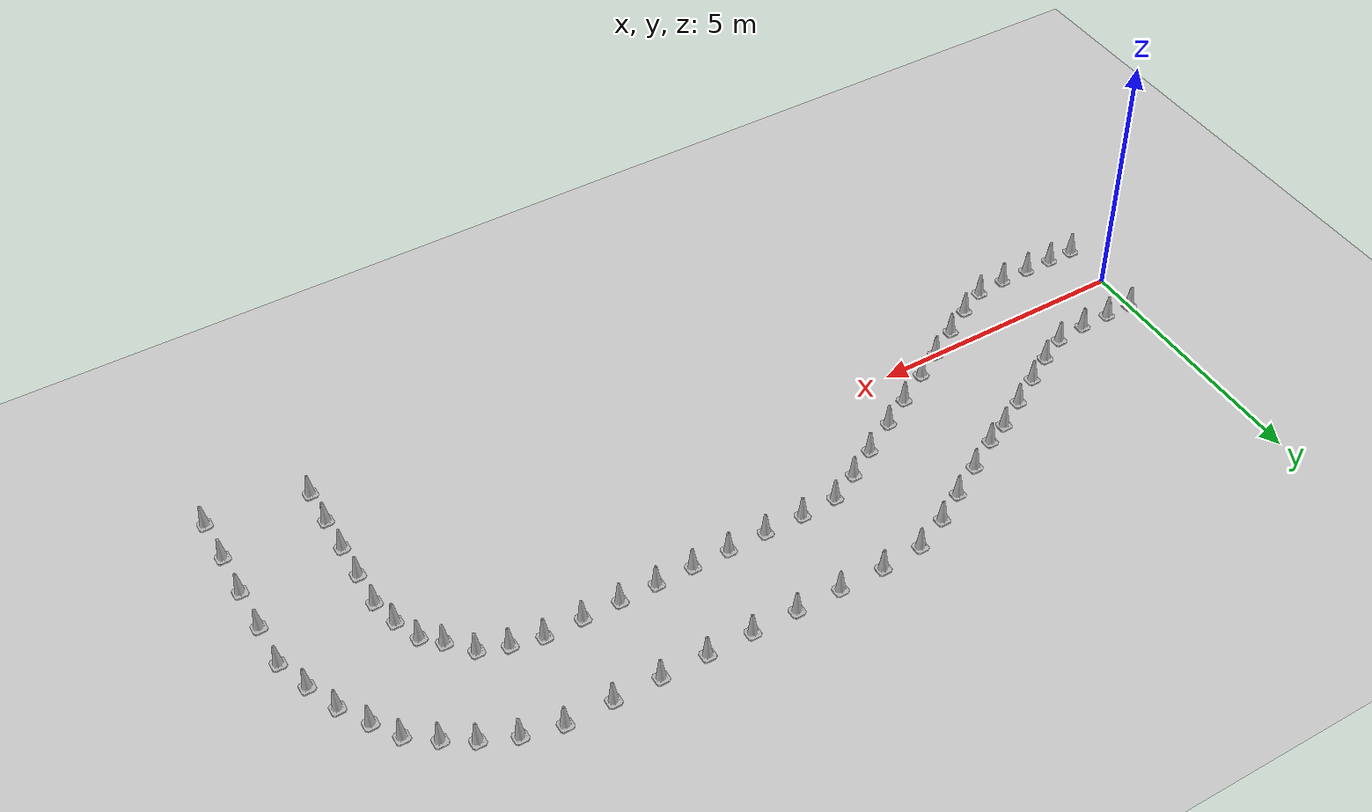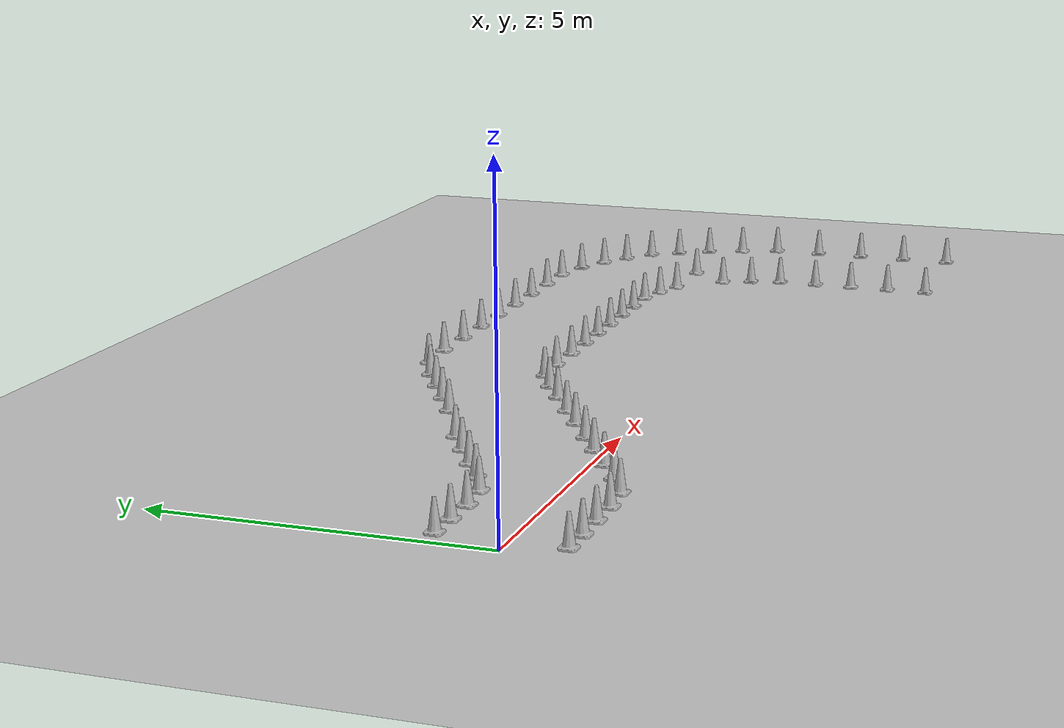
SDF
<sdf version="1.7">
 <world name="default">
  <light name="sun" type="directional">
   <pose>0 0 10 0 -0 0</pose>
   <diffuse>0.8 0.8 0.8 1</diffuse>
   <specular>0.2 0.2 0.2 1</specular>
   <attenuation>
    <range>1000</range>
    <constant>0.9</constant>
    <linear>0.01</linear>
    <quadratic>0.001</quadratic>
   </attenuation>
   <direction>-0.5 0.1 -0.9</direction>
   <spot><inner_angle>0</inner_angle><outer_angle>0</outer_angle><falloff>0</falloff></spot>
  </light>
  <gravity>0 0 -9.8</gravity>
  <magnetic_field>6e-06 2.3e-05 -4.2e-05</magnetic_field>
  <atmosphere type="adiabatic"/>
  <physics type="ode">
   <max_step_size>0.001</max_step_size>
   <real_time_factor>1</real_time_factor>
   <real_time_update_rate>1000</real_time_update_rate>
  </physics>
  <scene><ambient>0.4 0.4 0.4 1</ambient><background>0.7 0.7 0.7 1</background><shadows>1</shadows></scene>
  <spherical_coordinates>
   <surface_model>EARTH_WGS84</surface_model>
   <latitude_deg>0</latitude_deg>
   <longitude_deg>0</longitude_deg>
   <elevation>0</elevation>
   <heading_deg>0</heading_deg>
  </spherical_coordinates>
  <model name="Construction_Cone_b">
   <link name="link">
    <inertial>
     <inertia><ixx>1</ixx><ixy>0</ixy><ixz>0</ixz><iyy>1</iyy><iyz>0</iyz><izz>1</izz></inertia>
     <mass>1</mass>
    </inertial>
    <visual name="visual">
     <geometry>
      <mesh><scale>4.9 4.9 4.5</scale><uri>./construction_cone/meshes/construction_cone_b.dae</uri></mesh>
     </geometry>
     <material><shader type="pixel"/></material>
    </visual>
    <collision name="collision">
     <geometry>
      <mesh><uri>./construction_cone/meshes/construction_cone_b.dae</uri><scale>4.9 4.9 4.5</scale></mesh>
     </geometry>
     <surface>
      <friction>
       <ode><mu>1</mu><mu2>1</mu2><fdir1>0 0 0</fdir1><slip1>0</slip1><slip2>0</slip2></ode>
       <torsional>
        <coefficient>1</coefficient>
        <patch_radius>0</patch_radius>
        <surface_radius>0</surface_radius>
        <use_patch_radius>1</use_patch_radius>
        <ode><slip>0</slip></ode>
       </torsional>
      </friction>
      <bounce><restitution_coefficient>0</restitution_coefficient><threshold>1e+06</threshold></bounce>
      <contact>
       <collide_without_contact>0</collide_without_contact>
       <collide_without_contact_bitmask>1</collide_without_contact_bitmask>
       <collide_bitmask>1</collide_bitmask>
       <ode>
        <soft_cfm>0</soft_cfm>
        <soft_erp>0.2</soft_erp>
        <kp>1e+13</kp>
        <kd>1</kd>
        <max_vel>0.01</max_vel>
        <min_depth>0</min_depth>
       </ode>
       <bullet>
        <split_impulse>1</split_impulse>
        <split_impulse_penetration_threshold>-0.01</split_impulse_penetration_threshold>
        <soft_cfm>0</soft_cfm>
        <soft_erp>0.2</soft_erp>
        <kp>1e+13</kp>
        <kd>1</kd>
       </bullet>
      </contact>
     </surface>
    </collision>
   </link>
   <static>0</static>
   <pose>0.093537 -0.897019 0.1 0 0 0</pose>
  </model>
  <model name="Construction_Cone_b_0">
   <link name="link">
    <inertial>
     <inertia><ixx>1</ixx><ixy>0</ixy><ixz>0</ixz><iyy>1</iyy><iyz>0</iyz><izz>1</izz></inertia>
     <mass>1</mass>
    </inertial>
    <visual name="visual">
     <geometry>
      <mesh><scale>4.9 4.9 4.5</scale><uri>./construction_cone/meshes/construction_cone_b.dae</uri></mesh>
     </geometry>
     <material><shader type="pixel"/></material>
    </visual>
    <collision name="collision">
     <geometry>
      <mesh><uri>./construction_cone/meshes/construction_cone_b.dae</uri><scale>4.9 4.9 4.5</scale></mesh>
     </geometry>
     <surface>
      <friction>
       <ode><mu>1</mu><mu2>1</mu2><fdir1>0 0 0</fdir1><slip1>0</slip1><slip2>0</slip2></ode>
       <torsional>
        <coefficient>1</coefficient>
        <patch_radius>0</patch_radius>
        <surface_radius>0</surface_radius>
        <use_patch_radius>1</use_patch_radius>
        <ode><slip>0</slip></ode>
       </torsional>
      </friction>
      <bounce><restitution_coefficient>0</restitution_coefficient><threshold>1e+06</threshold></bounce>
      <contact>
       <collide_without_contact>0</collide_without_contact>
       <collide_without_contact_bitmask>1</collide_without_contact_bitmask>
       <collide_bitmask>1</collide_bitmask>
       <ode>
        <soft_cfm>0</soft_cfm>
        <soft_erp>0.2</soft_erp>
        <kp>1e+13</kp>
        <kd>1</kd>
        <max_vel>0.01</max_vel>
        <min_depth>0</min_depth>
       </ode>
       <bullet>
        <split_impulse>1</split_impulse>
        <split_impulse_penetration_threshold>-0.01</split_impulse_penetration_threshold>
        <soft_cfm>0</soft_cfm>
        <soft_erp>0.2</soft_erp>
        <kp>1e+13</kp>
        <kd>1</kd>
       </bullet>
      </contact>
     </surface>
    </collision>
   </link>
   <static>0</static>
   <pose>0.606486 -0.90196 0.1 0 0 0</pose>
  </model>
  <model name="Construction_Cone_b_1">
   <link name="link">
    <inertial>
     <inertia><ixx>1</ixx><ixy>0</ixy><ixz>0</ixz><iyy>1</iyy><iyz>0</iyz><izz>1</izz></inertia>
     <mass>1</mass>
    </inertial>
    <visual name="visual">
     <geometry>
      <mesh><scale>4.9 4.9 4.5</scale><uri>./construction_cone/meshes/construction_cone_b.dae</uri></mesh>
     </geometry>
     <material><shader type="pixel"/></material>
    </visual>
    <collision name="collision">
     <geometry>
      <mesh><uri>./construction_cone/meshes/construction_cone_b.dae</uri><scale>4.9 4.9 4.5</scale></mesh>
     </geometry>
     <surface>
      <friction>
       <ode><mu>1</mu><mu2>1</mu2><fdir1>0 0 0</fdir1><slip1>0</slip1><slip2>0</slip2></ode>
       <torsional>
        <coefficient>1</coefficient>
        <patch_radius>0</patch_radius>
        <surface_radius>0</surface_radius>
        <use_patch_radius>1</use_patch_radius>
        <ode><slip>0</slip></ode>
       </torsional>
      </friction>
      <bounce><restitution_coefficient>0</restitution_coefficient><threshold>1e+06</threshold></bounce>
      <contact>
       <collide_without_contact>0</collide_without_contact>
       <collide_without_contact_bitmask>1</collide_without_contact_bitmask>
       <collide_bitmask>1</collide_bitmask>
       <ode>
        <soft_cfm>0</soft_cfm>
        <soft_erp>0.2</soft_erp>
        <kp>1e+13</kp>
        <kd>1</kd>
        <max_vel>0.01</max_vel>
        <min_depth>0</min_depth>
       </ode>
       <bullet>
        <split_impulse>1</split_impulse>
        <split_impulse_penetration_threshold>-0.01</split_impulse_penetration_threshold>
        <soft_cfm>0</soft_cfm>
        <soft_erp>0.2</soft_erp>
        <kp>1e+13</kp>
        <kd>1</kd>
       </bullet>
      </contact>
     </surface>
    </collision>
   </link>
   <static>0</static>
   <pose>1.16003 -0.900212 0.1 0 0 0</pose>
  </model>
  <model name="Construction_Cone_y">
   <link name="link">
    <inertial>
     <inertia><ixx>1</ixx><ixy>0</ixy><ixz>0</ixz><iyy>1</iyy><iyz>0</iyz><izz>1</izz></inertia>
     <mass>1</mass>
    </inertial>
    <visual name="visual">
     <geometry>
      <mesh><scale>4.9 4.9 4.5</scale><uri>./construction_cone/meshes/construction_cone_y.dae</uri></mesh>
     </geometry>
     <material><shader type="pixel"/></material>
    </visual>
    <collision name="collision">
     <geometry>
      <mesh><uri>./construction_cone/meshes/construction_cone_y.dae</uri><scale>4.9 4.9 4.5</scale></mesh>
     </geometry>
     <surface>
      <friction>
       <ode><mu>1</mu><mu2>1</mu2><fdir1>0 0 0</fdir1><slip1>0</slip1><slip2>0</slip2></ode>
       <torsional>
        <coefficient>1</coefficient>
        <patch_radius>0</patch_radius>
        <surface_radius>0</surface_radius>
        <use_patch_radius>1</use_patch_radius>
        <ode><slip>0</slip></ode>
       </torsional>
      </friction>
      <bounce><restitution_coefficient>0</restitution_coefficient><threshold>1e+06</threshold></bounce>
      <contact>
       <collide_without_contact>0</collide_without_contact>
       <collide_without_contact_bitmask>1</collide_without_contact_bitmask>
       <collide_bitmask>1</collide_bitmask>
       <ode>
        <soft_cfm>0</soft_cfm>
        <soft_erp>0.2</soft_erp>
        <kp>1e+13</kp>
        <kd>1</kd>
        <max_vel>0.01</max_vel>
        <min_depth>0</min_depth>
       </ode>
       <bullet>
        <split_impulse>1</split_impulse>
        <split_impulse_penetration_threshold>-0.01</split_impulse_penetration_threshold>
        <soft_cfm>0</soft_cfm>
        <soft_erp>0.2</soft_erp>
        <kp>1e+13</kp>
        <kd>1</kd>
       </bullet>
      </contact>
     </surface>
    </collision>
   </link>
   <static>0</static>
   <pose>0.091565 0.900771 0.1 0 0 0</pose>
  </model>
  <model name="Construction_Cone_b_2">
   <link name="link">
    <inertial>
     <inertia><ixx>1</ixx><ixy>0</ixy><ixz>0</ixz><iyy>1</iyy><iyz>0</iyz><izz>1</izz></inertia>
     <mass>1</mass>
    </inertial>
    <visual name="visual">
     <geometry>
      <mesh><scale>4.9 4.9 4.5</scale><uri>./construction_cone/meshes/construction_cone_b.dae</uri></mesh>
     </geometry>
     <material><shader type="pixel"/></material>
    </visual>
    <collision name="collision">
     <geometry>
      <mesh><uri>./construction_cone/meshes/construction_cone_b.dae</uri><scale>4.9 4.9 4.5</scale></mesh>
     </geometry>
     <surface>
      <friction>
       <ode><mu>1</mu><mu2>1</mu2><fdir1>0 0 0</fdir1><slip1>0</slip1><slip2>0</slip2></ode>
       <torsional>
        <coefficient>1</coefficient>
        <patch_radius>0</patch_radius>
        <surface_radius>0</surface_radius>
        <use_patch_radius>1</use_patch_radius>
        <ode><slip>0</slip></ode>
       </torsional>
      </friction>
      <bounce><restitution_coefficient>0</restitution_coefficient><threshold>1e+06</threshold></bounce>
      <contact>
       <collide_without_contact>0</collide_without_contact>
       <collide_without_contact_bitmask>1</collide_without_contact_bitmask>
       <collide_bitmask>1</collide_bitmask>
       <ode>
        <soft_cfm>0</soft_cfm>
        <soft_erp>0.2</soft_erp>
        <kp>1e+13</kp>
        <kd>1</kd>
        <max_vel>0.01</max_vel>
        <min_depth>0</min_depth>
       </ode>
       <bullet>
        <split_impulse>1</split_impulse>
        <split_impulse_penetration_threshold>-0.01</split_impulse_penetration_threshold>
        <soft_cfm>0</soft_cfm>
        <soft_erp>0.2</soft_erp>
        <kp>1e+13</kp>
        <kd>1</kd>
       </bullet>
      </contact>
     </surface>
    </collision>
   </link>
   <static>0</static>
   <pose>1.73023 -0.902282 0.1 0 0 0</pose>
  </model>
  <model name="Construction_Cone_b_3">
   <link name="link">
    <inertial>
     <inertia><ixx>1</ixx><ixy>0</ixy><ixz>0</ixz><iyy>1</iyy><iyz>0</iyz><izz>1</izz></inertia>
     <mass>1</mass>
    </inertial>
    <visual name="visual">
     <geometry>
      <mesh><scale>4.9 4.9 4.5</scale><uri>./construction_cone/meshes/construction_cone_b.dae</uri></mesh>
     </geometry>
     <material><shader type="pixel"/></material>
    </visual>
    <collision name="collision">
     <geometry>
      <mesh><uri>./construction_cone/meshes/construction_cone_b.dae</uri><scale>4.9 4.9 4.5</scale></mesh>
     </geometry>
     <surface>
      <friction>
       <ode><mu>1</mu><mu2>1</mu2><fdir1>0 0 0</fdir1><slip1>0</slip1><slip2>0</slip2></ode>
       <torsional>
        <coefficient>1</coefficient>
        <patch_radius>0</patch_radius>
        <surface_radius>0</surface_radius>
        <use_patch_radius>1</use_patch_radius>
        <ode><slip>0</slip></ode>
       </torsional>
      </friction>
      <bounce><restitution_coefficient>0</restitution_coefficient><threshold>1e+06</threshold></bounce>
      <contact>
       <collide_without_contact>0</collide_without_contact>
       <collide_without_contact_bitmask>1</collide_without_contact_bitmask>
       <collide_bitmask>1</collide_bitmask>
       <ode>
        <soft_cfm>0</soft_cfm>
        <soft_erp>0.2</soft_erp>
        <kp>1e+13</kp>
        <kd>1</kd>
        <max_vel>0.01</max_vel>
        <min_depth>0</min_depth>
       </ode>
       <bullet>
        <split_impulse>1</split_impulse>
        <split_impulse_penetration_threshold>-0.01</split_impulse_penetration_threshold>
        <soft_cfm>0</soft_cfm>
        <soft_erp>0.2</soft_erp>
        <kp>1e+13</kp>
        <kd>1</kd>
       </bullet>
      </contact>
     </surface>
    </collision>
   </link>
   <static>0</static>
   <pose>2.31119 -0.853844 0.1 0 0 0</pose>
  </model>
  <model name="Construction_Cone_b_4">
   <link name="link">
    <inertial>
     <inertia><ixx>1</ixx><ixy>0</ixy><ixz>0</ixz><iyy>1</iyy><iyz>0</iyz><izz>1</izz></inertia>
     <mass>1</mass>
    </inertial>
    <visual name="visual">
     <geometry>
      <mesh><scale>4.9 4.9 4.5</scale><uri>./construction_cone/meshes/construction_cone_b.dae</uri></mesh>
     </geometry>
     <material><shader type="pixel"/></material>
    </visual>
    <collision name="collision">
     <geometry>
      <mesh><uri>./construction_cone/meshes/construction_cone_b.dae</uri><scale>4.9 4.9 4.5</scale></mesh>
     </geometry>
     <surface>
      <friction>
       <ode><mu>1</mu><mu2>1</mu2><fdir1>0 0 0</fdir1><slip1>0</slip1><slip2>0</slip2></ode>
       <torsional>
        <coefficient>1</coefficient>
        <patch_radius>0</patch_radius>
        <surface_radius>0</surface_radius>
        <use_patch_radius>1</use_patch_radius>
        <ode><slip>0</slip></ode>
       </torsional>
      </friction>
      <bounce><restitution_coefficient>0</restitution_coefficient><threshold>1e+06</threshold></bounce>
      <contact>
       <collide_without_contact>0</collide_without_contact>
       <collide_without_contact_bitmask>1</collide_without_contact_bitmask>
       <collide_bitmask>1</collide_bitmask>
       <ode>
        <soft_cfm>0</soft_cfm>
        <soft_erp>0.2</soft_erp>
        <kp>1e+13</kp>
        <kd>1</kd>
        <max_vel>0.01</max_vel>
        <min_depth>0</min_depth>
       </ode>
       <bullet>
        <split_impulse>1</split_impulse>
        <split_impulse_penetration_threshold>-0.01</split_impulse_penetration_threshold>
        <soft_cfm>0</soft_cfm>
        <soft_erp>0.2</soft_erp>
        <kp>1e+13</kp>
        <kd>1</kd>
       </bullet>
      </contact>
     </surface>
    </collision>
   </link>
   <static>0</static>
   <pose>2.84787 -0.595042 0.1 0 0 0</pose>
  </model>
  <model name="Construction_Cone_b_5">
   <link name="link">
    <inertial>
     <inertia><ixx>1</ixx><ixy>0</ixy><ixz>0</ixz><iyy>1</iyy><iyz>0</iyz><izz>1</izz></inertia>
     <mass>1</mass>
    </inertial>
    <visual name="visual">
     <geometry>
      <mesh><scale>4.9 4.9 4.5</scale><uri>./construction_cone/meshes/construction_cone_b.dae</uri></mesh>
     </geometry>
     <material><shader type="pixel"/></material>
    </visual>
    <collision name="collision">
     <geometry>
      <mesh><uri>./construction_cone/meshes/construction_cone_b.dae</uri><scale>4.9 4.9 4.5</scale></mesh>
     </geometry>
     <surface>
      <friction>
       <ode><mu>1</mu><mu2>1</mu2><fdir1>0 0 0</fdir1><slip1>0</slip1><slip2>0</slip2></ode>
       <torsional>
        <coefficient>1</coefficient>
        <patch_radius>0</patch_radius>
        <surface_radius>0</surface_radius>
        <use_patch_radius>1</use_patch_radius>
        <ode><slip>0</slip></ode>
       </torsional>
      </friction>
      <bounce><restitution_coefficient>0</restitution_coefficient><threshold>1e+06</threshold></bounce>
      <contact>
       <collide_without_contact>0</collide_without_contact>
       <collide_without_contact_bitmask>1</collide_without_contact_bitmask>
       <collide_bitmask>1</collide_bitmask>
       <ode>
        <soft_cfm>0</soft_cfm>
        <soft_erp>0.2</soft_erp>
        <kp>1e+13</kp>
        <kd>1</kd>
        <max_vel>0.01</max_vel>
        <min_depth>0</min_depth>
       </ode>
       <bullet>
        <split_impulse>1</split_impulse>
        <split_impulse_penetration_threshold>-0.01</split_impulse_penetration_threshold>
        <soft_cfm>0</soft_cfm>
        <soft_erp>0.2</soft_erp>
        <kp>1e+13</kp>
        <kd>1</kd>
       </bullet>
      </contact>
     </surface>
    </collision>
   </link>
   <static>0</static>
   <pose>3.39406 -0.275779 0.1 0 0 0</pose>
  </model>
  <model name="Construction_Cone_b_6">
   <link name="link">
    <inertial>
     <inertia><ixx>1</ixx><ixy>0</ixy><ixz>0</ixz><iyy>1</iyy><iyz>0</iyz><izz>1</izz></inertia>
     <mass>1</mass>
    </inertial>
    <visual name="visual">
     <geometry>
      <mesh><scale>4.9 4.9 4.5</scale><uri>./construction_cone/meshes/construction_cone_b.dae</uri></mesh>
     </geometry>
     <material><shader type="pixel"/></material>
    </visual>
    <collision name="collision">
     <geometry>
      <mesh><uri>./construction_cone/meshes/construction_cone_b.dae</uri><scale>4.9 4.9 4.5</scale></mesh>
     </geometry>
     <surface>
      <friction>
       <ode><mu>1</mu><mu2>1</mu2><fdir1>0 0 0</fdir1><slip1>0</slip1><slip2>0</slip2></ode>
       <torsional>
        <coefficient>1</coefficient>
        <patch_radius>0</patch_radius>
        <surface_radius>0</surface_radius>
        <use_patch_radius>1</use_patch_radius>
        <ode><slip>0</slip></ode>
       </torsional>
      </friction>
      <bounce><restitution_coefficient>0</restitution_coefficient><threshold>1e+06</threshold></bounce>
      <contact>
       <collide_without_contact>0</collide_without_contact>
       <collide_without_contact_bitmask>1</collide_without_contact_bitmask>
       <collide_bitmask>1</collide_bitmask>
       <ode>
        <soft_cfm>0</soft_cfm>
        <soft_erp>0.2</soft_erp>
        <kp>1e+13</kp>
        <kd>1</kd>
        <max_vel>0.01</max_vel>
        <min_depth>0</min_depth>
       </ode>
       <bullet>
        <split_impulse>1</split_impulse>
        <split_impulse_penetration_threshold>-0.01</split_impulse_penetration_threshold>
        <soft_cfm>0</soft_cfm>
        <soft_erp>0.2</soft_erp>
        <kp>1e+13</kp>
        <kd>1</kd>
       </bullet>
      </contact>
     </surface>
    </collision>
   </link>
   <static>0</static>
   <pose>5.14298 0.744444 0.1 0 0 0</pose>
  </model>
  <model name="Construction_Cone_b_7">
   <link name="link">
    <inertial>
     <inertia><ixx>1</ixx><ixy>0</ixy><ixz>0</ixz><iyy>1</iyy><iyz>0</iyz><izz>1</izz></inertia>
     <mass>1</mass>
    </inertial>
    <visual name="visual">
     <geometry>
      <mesh><scale>4.9 4.9 4.5</scale><uri>./construction_cone/meshes/construction_cone_b.dae</uri></mesh>
     </geometry>
     <material><shader type="pixel"/></material>
    </visual>
    <collision name="collision">
     <geometry>
      <mesh><uri>./construction_cone/meshes/construction_cone_b.dae</uri><scale>4.9 4.9 4.5</scale></mesh>
     </geometry>
     <surface>
      <friction>
       <ode><mu>1</mu><mu2>1</mu2><fdir1>0 0 0</fdir1><slip1>0</slip1><slip2>0</slip2></ode>
       <torsional>
        <coefficient>1</coefficient>
        <patch_radius>0</patch_radius>
        <surface_radius>0</surface_radius>
        <use_patch_radius>1</use_patch_radius>
        <ode><slip>0</slip></ode>
       </torsional>
      </friction>
      <bounce><restitution_coefficient>0</restitution_coefficient><threshold>1e+06</threshold></bounce>
      <contact>
       <collide_without_contact>0</collide_without_contact>
       <collide_without_contact_bitmask>1</collide_without_contact_bitmask>
       <collide_bitmask>1</collide_bitmask>
       <ode>
        <soft_cfm>0</soft_cfm>
        <soft_erp>0.2</soft_erp>
        <kp>1e+13</kp>
        <kd>1</kd>
        <max_vel>0.01</max_vel>
        <min_depth>0</min_depth>
       </ode>
       <bullet>
        <split_impulse>1</split_impulse>
        <split_impulse_penetration_threshold>-0.01</split_impulse_penetration_threshold>
        <soft_cfm>0</soft_cfm>
        <soft_erp>0.2</soft_erp>
        <kp>1e+13</kp>
        <kd>1</kd>
       </bullet>
      </contact>
     </surface>
    </collision>
   </link>
   <static>0</static>
   <pose>3.98269 0.070598 0.1 0 0 0</pose>
  </model>
  <model name="Construction_Cone_b_8">
   <link name="link">
    <inertial>
     <inertia><ixx>1</ixx><ixy>0</ixy><ixz>0</ixz><iyy>1</iyy><iyz>0</iyz><izz>1</izz></inertia>
     <mass>1</mass>
    </inertial>
    <visual name="visual">
     <geometry>
      <mesh><scale>4.9 4.9 4.5</scale><uri>./construction_cone/meshes/construction_cone_b.dae</uri></mesh>
     </geometry>
     <material><shader type="pixel"/></material>
    </visual>
    <collision name="collision">
     <geometry>
      <mesh><uri>./construction_cone/meshes/construction_cone_b.dae</uri><scale>4.9 4.9 4.5</scale></mesh>
     </geometry>
     <surface>
      <friction>
       <ode><mu>1</mu><mu2>1</mu2><fdir1>0 0 0</fdir1><slip1>0</slip1><slip2>0</slip2></ode>
       <torsional>
        <coefficient>1</coefficient>
        <patch_radius>0</patch_radius>
        <surface_radius>0</surface_radius>
        <use_patch_radius>1</use_patch_radius>
        <ode><slip>0</slip></ode>
       </torsional>
      </friction>
      <bounce><restitution_coefficient>0</restitution_coefficient><threshold>1e+06</threshold></bounce>
      <contact>
       <collide_without_contact>0</collide_without_contact>
       <collide_without_contact_bitmask>1</collide_without_contact_bitmask>
       <collide_bitmask>1</collide_bitmask>
       <ode>
        <soft_cfm>0</soft_cfm>
        <soft_erp>0.2</soft_erp>
        <kp>1e+13</kp>
        <kd>1</kd>
        <max_vel>0.01</max_vel>
        <min_depth>0</min_depth>
       </ode>
       <bullet>
        <split_impulse>1</split_impulse>
        <split_impulse_penetration_threshold>-0.01</split_impulse_penetration_threshold>
        <soft_cfm>0</soft_cfm>
        <soft_erp>0.2</soft_erp>
        <kp>1e+13</kp>
        <kd>1</kd>
       </bullet>
      </contact>
     </surface>
    </collision>
   </link>
   <static>0</static>
   <pose>4.51383 0.378539 0.1 0 0 0</pose>
  </model>
  <model name="Construction_Cone_y_0">
   <link name="link">
    <inertial>
     <inertia><ixx>1</ixx><ixy>0</ixy><ixz>0</ixz><iyy>1</iyy><iyz>0</iyz><izz>1</izz></inertia>
     <mass>1</mass>
    </inertial>
    <visual name="visual">
     <geometry>
      <mesh><scale>4.9 4.9 4.5</scale><uri>./construction_cone/meshes/construction_cone_y.dae</uri></mesh>
     </geometry>
     <material><shader type="pixel"/></material>
    </visual>
    <collision name="collision">
     <geometry>
      <mesh><uri>./construction_cone/meshes/construction_cone_y.dae</uri><scale>4.9 4.9 4.5</scale></mesh>
     </geometry>
     <surface>
      <friction>
       <ode><mu>1</mu><mu2>1</mu2><fdir1>0 0 0</fdir1><slip1>0</slip1><slip2>0</slip2></ode>
       <torsional>
        <coefficient>1</coefficient>
        <patch_radius>0</patch_radius>
        <surface_radius>0</surface_radius>
        <use_patch_radius>1</use_patch_radius>
        <ode><slip>0</slip></ode>
       </torsional>
      </friction>
      <bounce><restitution_coefficient>0</restitution_coefficient><threshold>1e+06</threshold></bounce>
      <contact>
       <collide_without_contact>0</collide_without_contact>
       <collide_without_contact_bitmask>1</collide_without_contact_bitmask>
       <collide_bitmask>1</collide_bitmask>
       <ode>
        <soft_cfm>0</soft_cfm>
        <soft_erp>0.2</soft_erp>
        <kp>1e+13</kp>
        <kd>1</kd>
        <max_vel>0.01</max_vel>
        <min_depth>0</min_depth>
       </ode>
       <bullet>
        <split_impulse>1</split_impulse>
        <split_impulse_penetration_threshold>-0.01</split_impulse_penetration_threshold>
        <soft_cfm>0</soft_cfm>
        <soft_erp>0.2</soft_erp>
        <kp>1e+13</kp>
        <kd>1</kd>
       </bullet>
      </contact>
     </surface>
    </collision>
   </link>
   <static>0</static>
   <pose>0.622219 0.89678 0.1 0 0 0</pose>
  </model>
  <model name="Construction_Cone_y_1">
   <link name="link">
    <inertial>
     <inertia><ixx>1</ixx><ixy>0</ixy><ixz>0</ixz><iyy>1</iyy><iyz>0</iyz><izz>1</izz></inertia>
     <mass>1</mass>
    </inertial>
    <visual name="visual">
     <geometry>
      <mesh><scale>4.9 4.9 4.5</scale><uri>./construction_cone/meshes/construction_cone_y.dae</uri></mesh>
     </geometry>
     <material><shader type="pixel"/></material>
    </visual>
    <collision name="collision">
     <geometry>
      <mesh><uri>./construction_cone/meshes/construction_cone_y.dae</uri><scale>4.9 4.9 4.5</scale></mesh>
     </geometry>
     <surface>
      <friction>
       <ode><mu>1</mu><mu2>1</mu2><fdir1>0 0 0</fdir1><slip1>0</slip1><slip2>0</slip2></ode>
       <torsional>
        <coefficient>1</coefficient>
        <patch_radius>0</patch_radius>
        <surface_radius>0</surface_radius>
        <use_patch_radius>1</use_patch_radius>
        <ode><slip>0</slip></ode>
       </torsional>
      </friction>
      <bounce><restitution_coefficient>0</restitution_coefficient><threshold>1e+06</threshold></bounce>
      <contact>
       <collide_without_contact>0</collide_without_contact>
       <collide_without_contact_bitmask>1</collide_without_contact_bitmask>
       <collide_bitmask>1</collide_bitmask>
       <ode>
        <soft_cfm>0</soft_cfm>
        <soft_erp>0.2</soft_erp>
        <kp>1e+13</kp>
        <kd>1</kd>
        <max_vel>0.01</max_vel>
        <min_depth>0</min_depth>
       </ode>
       <bullet>
        <split_impulse>1</split_impulse>
        <split_impulse_penetration_threshold>-0.01</split_impulse_penetration_threshold>
        <soft_cfm>0</soft_cfm>
        <soft_erp>0.2</soft_erp>
        <kp>1e+13</kp>
        <kd>1</kd>
       </bullet>
      </contact>
     </surface>
    </collision>
   </link>
   <static>0</static>
   <pose>1.20445 0.898871 0.1 0 0 0</pose>
  </model>
  <model name="Construction_Cone_y_2">
   <link name="link">
    <inertial>
     <inertia><ixx>1</ixx><ixy>0</ixy><ixz>0</ixz><iyy>1</iyy><iyz>0</iyz><izz>1</izz></inertia>
     <mass>1</mass>
    </inertial>
    <visual name="visual">
     <geometry>
      <mesh><scale>4.9 4.9 4.5</scale><uri>./construction_cone/meshes/construction_cone_y.dae</uri></mesh>
     </geometry>
     <material><shader type="pixel"/></material>
    </visual>
    <collision name="collision">
     <geometry>
      <mesh><uri>./construction_cone/meshes/construction_cone_y.dae</uri><scale>4.9 4.9 4.5</scale></mesh>
     </geometry>
     <surface>
      <friction>
       <ode><mu>1</mu><mu2>1</mu2><fdir1>0 0 0</fdir1><slip1>0</slip1><slip2>0</slip2></ode>
       <torsional>
        <coefficient>1</coefficient>
        <patch_radius>0</patch_radius>
        <surface_radius>0</surface_radius>
        <use_patch_radius>1</use_patch_radius>
        <ode><slip>0</slip></ode>
       </torsional>
      </friction>
      <bounce><restitution_coefficient>0</restitution_coefficient><threshold>1e+06</threshold></bounce>
      <contact>
       <collide_without_contact>0</collide_without_contact>
       <collide_without_contact_bitmask>1</collide_without_contact_bitmask>
       <collide_bitmask>1</collide_bitmask>
       <ode>
        <soft_cfm>0</soft_cfm>
        <soft_erp>0.2</soft_erp>
        <kp>1e+13</kp>
        <kd>1</kd>
        <max_vel>0.01</max_vel>
        <min_depth>0</min_depth>
       </ode>
       <bullet>
        <split_impulse>1</split_impulse>
        <split_impulse_penetration_threshold>-0.01</split_impulse_penetration_threshold>
        <soft_cfm>0</soft_cfm>
        <soft_erp>0.2</soft_erp>
        <kp>1e+13</kp>
        <kd>1</kd>
       </bullet>
      </contact>
     </surface>
    </collision>
   </link>
   <static>0</static>
   <pose>1.80702 0.965041 0.1 0 0 0</pose>
  </model>
  <model name="Construction_Cone_y_3">
   <link name="link">
    <inertial>
     <inertia><ixx>1</ixx><ixy>0</ixy><ixz>0</ixz><iyy>1</iyy><iyz>0</iyz><izz>1</izz></inertia>
     <mass>1</mass>
    </inertial>
    <visual name="visual">
     <geometry>
      <mesh><scale>4.9 4.9 4.5</scale><uri>./construction_cone/meshes/construction_cone_y.dae</uri></mesh>
     </geometry>
     <material><shader type="pixel"/></material>
    </visual>
    <collision name="collision">
     <geometry>
      <mesh><uri>./construction_cone/meshes/construction_cone_y.dae</uri><scale>4.9 4.9 4.5</scale></mesh>
     </geometry>
     <surface>
      <friction>
       <ode><mu>1</mu><mu2>1</mu2><fdir1>0 0 0</fdir1><slip1>0</slip1><slip2>0</slip2></ode>
       <torsional>
        <coefficient>1</coefficient>
        <patch_radius>0</patch_radius>
        <surface_radius>0</surface_radius>
        <use_patch_radius>1</use_patch_radius>
        <ode><slip>0</slip></ode>
       </torsional>
      </friction>
      <bounce><restitution_coefficient>0</restitution_coefficient><threshold>1e+06</threshold></bounce>
      <contact>
       <collide_without_contact>0</collide_without_contact>
       <collide_without_contact_bitmask>1</collide_without_contact_bitmask>
       <collide_bitmask>1</collide_bitmask>
       <ode>
        <soft_cfm>0</soft_cfm>
        <soft_erp>0.2</soft_erp>
        <kp>1e+13</kp>
        <kd>1</kd>
        <max_vel>0.01</max_vel>
        <min_depth>0</min_depth>
       </ode>
       <bullet>
        <split_impulse>1</split_impulse>
        <split_impulse_penetration_threshold>-0.01</split_impulse_penetration_threshold>
        <soft_cfm>0</soft_cfm>
        <soft_erp>0.2</soft_erp>
        <kp>1e+13</kp>
        <kd>1</kd>
       </bullet>
      </contact>
     </surface>
    </collision>
   </link>
   <static>0</static>
   <pose>2.3205 1.21296 0.1 0 0 0</pose>
  </model>
  <model name="Construction_Cone_y_5">
   <link name="link">
    <inertial>
     <inertia><ixx>1</ixx><ixy>0</ixy><ixz>0</ixz><iyy>1</iyy><iyz>0</iyz><izz>1</izz></inertia>
     <mass>1</mass>
    </inertial>
    <visual name="visual">
     <geometry>
      <mesh><scale>4.9 4.9 4.5</scale><uri>./construction_cone/meshes/construction_cone_y.dae</uri></mesh>
     </geometry>
     <material><shader type="pixel"/></material>
    </visual>
    <collision name="collision">
     <geometry>
      <mesh><uri>./construction_cone/meshes/construction_cone_y.dae</uri><scale>4.9 4.9 4.5</scale></mesh>
     </geometry>
     <surface>
      <friction>
       <ode><mu>1</mu><mu2>1</mu2><fdir1>0 0 0</fdir1><slip1>0</slip1><slip2>0</slip2></ode>
       <torsional>
        <coefficient>1</coefficient>
        <patch_radius>0</patch_radius>
        <surface_radius>0</surface_radius>
        <use_patch_radius>1</use_patch_radius>
        <ode><slip>0</slip></ode>
       </torsional>
      </friction>
      <bounce><restitution_coefficient>0</restitution_coefficient><threshold>1e+06</threshold></bounce>
      <contact>
       <collide_without_contact>0</collide_without_contact>
       <collide_without_contact_bitmask>1</collide_without_contact_bitmask>
       <collide_bitmask>1</collide_bitmask>
       <ode>
        <soft_cfm>0</soft_cfm>
        <soft_erp>0.2</soft_erp>
        <kp>1e+13</kp>
        <kd>1</kd>
        <max_vel>0.01</max_vel>
        <min_depth>0</min_depth>
       </ode>
       <bullet>
        <split_impulse>1</split_impulse>
        <split_impulse_penetration_threshold>-0.01</split_impulse_penetration_threshold>
        <soft_cfm>0</soft_cfm>
        <soft_erp>0.2</soft_erp>
        <kp>1e+13</kp>
        <kd>1</kd>
       </bullet>
      </contact>
     </surface>
    </collision>
   </link>
   <static>0</static>
   <pose>2.85114 1.52267 0.1 0 0 0</pose>
  </model>
  <model name="Construction_Cone_y_6">
   <link name="link">
    <inertial>
     <inertia><ixx>1</ixx><ixy>0</ixy><ixz>0</ixz><iyy>1</iyy><iyz>0</iyz><izz>1</izz></inertia>
     <mass>1</mass>
    </inertial>
    <visual name="visual">
     <geometry>
      <mesh><scale>4.9 4.9 4.5</scale><uri>./construction_cone/meshes/construction_cone_y.dae</uri></mesh>
     </geometry>
     <material><shader type="pixel"/></material>
    </visual>
    <collision name="collision">
     <geometry>
      <mesh><uri>./construction_cone/meshes/construction_cone_y.dae</uri><scale>4.9 4.9 4.5</scale></mesh>
     </geometry>
     <surface>
      <friction>
       <ode><mu>1</mu><mu2>1</mu2><fdir1>0 0 0</fdir1><slip1>0</slip1><slip2>0</slip2></ode>
       <torsional>
        <coefficient>1</coefficient>
        <patch_radius>0</patch_radius>
        <surface_radius>0</surface_radius>
        <use_patch_radius>1</use_patch_radius>
        <ode><slip>0</slip></ode>
       </torsional>
      </friction>
      <bounce><restitution_coefficient>0</restitution_coefficient><threshold>1e+06</threshold></bounce>
      <contact>
       <collide_without_contact>0</collide_without_contact>
       <collide_without_contact_bitmask>1</collide_without_contact_bitmask>
       <collide_bitmask>1</collide_bitmask>
       <ode>
        <soft_cfm>0</soft_cfm>
        <soft_erp>0.2</soft_erp>
        <kp>1e+13</kp>
        <kd>1</kd>
        <max_vel>0.01</max_vel>
        <min_depth>0</min_depth>
       </ode>
       <bullet>
        <split_impulse>1</split_impulse>
        <split_impulse_penetration_threshold>-0.01</split_impulse_penetration_threshold>
        <soft_cfm>0</soft_cfm>
        <soft_erp>0.2</soft_erp>
        <kp>1e+13</kp>
        <kd>1</kd>
       </bullet>
      </contact>
     </surface>
    </collision>
   </link>
   <static>0</static>
   <pose>3.41707 1.85526 0.1 0 0 0</pose>
  </model>
  <model name="Construction_Cone_y_7">
   <link name="link">
    <inertial>
     <inertia><ixx>1</ixx><ixy>0</ixy><ixz>0</ixz><iyy>1</iyy><iyz>0</iyz><izz>1</izz></inertia>
     <mass>1</mass>
    </inertial>
    <visual name="visual">
     <geometry>
      <mesh><scale>4.9 4.9 4.5</scale><uri>./construction_cone/meshes/construction_cone_y.dae</uri></mesh>
     </geometry>
     <material><shader type="pixel"/></material>
    </visual>
    <collision name="collision">
     <geometry>
      <mesh><uri>./construction_cone/meshes/construction_cone_y.dae</uri><scale>4.9 4.9 4.5</scale></mesh>
     </geometry>
     <surface>
      <friction>
       <ode><mu>1</mu><mu2>1</mu2><fdir1>0 0 0</fdir1><slip1>0</slip1><slip2>0</slip2></ode>
       <torsional>
        <coefficient>1</coefficient>
        <patch_radius>0</patch_radius>
        <surface_radius>0</surface_radius>
        <use_patch_radius>1</use_patch_radius>
        <ode><slip>0</slip></ode>
       </torsional>
      </friction>
      <bounce><restitution_coefficient>0</restitution_coefficient><threshold>1e+06</threshold></bounce>
      <contact>
       <collide_without_contact>0</collide_without_contact>
       <collide_without_contact_bitmask>1</collide_without_contact_bitmask>
       <collide_bitmask>1</collide_bitmask>
       <ode>
        <soft_cfm>0</soft_cfm>
        <soft_erp>0.2</soft_erp>
        <kp>1e+13</kp>
        <kd>1</kd>
        <max_vel>0.01</max_vel>
        <min_depth>0</min_depth>
       </ode>
       <bullet>
        <split_impulse>1</split_impulse>
        <split_impulse_penetration_threshold>-0.01</split_impulse_penetration_threshold>
        <soft_cfm>0</soft_cfm>
        <soft_erp>0.2</soft_erp>
        <kp>1e+13</kp>
        <kd>1</kd>
       </bullet>
      </contact>
     </surface>
    </collision>
   </link>
   <static>0</static>
   <pose>3.97498 2.18035 0.1 0 0 0</pose>
  </model>
  <model name="Construction_Cone_b_9">
   <link name="link">
    <inertial>
     <inertia><ixx>1</ixx><ixy>0</ixy><ixz>0</ixz><iyy>1</iyy><iyz>0</iyz><izz>1</izz></inertia>
     <mass>1</mass>
    </inertial>
    <visual name="visual">
     <geometry>
      <mesh><scale>4.9 4.9 4.5</scale><uri>./construction_cone/meshes/construction_cone_b.dae</uri></mesh>
     </geometry>
     <material><shader type="pixel"/></material>
    </visual>
    <collision name="collision">
     <geometry>
      <mesh><uri>./construction_cone/meshes/construction_cone_b.dae</uri><scale>4.9 4.9 4.5</scale></mesh>
     </geometry>
     <surface>
      <friction>
       <ode><mu>1</mu><mu2>1</mu2><fdir1>0 0 0</fdir1><slip1>0</slip1><slip2>0</slip2></ode>
       <torsional>
        <coefficient>1</coefficient>
        <patch_radius>0</patch_radius>
        <surface_radius>0</surface_radius>
        <use_patch_radius>1</use_patch_radius>
        <ode><slip>0</slip></ode>
       </torsional>
      </friction>
      <bounce><restitution_coefficient>0</restitution_coefficient><threshold>1e+06</threshold></bounce>
      <contact>
       <collide_without_contact>0</collide_without_contact>
       <collide_without_contact_bitmask>1</collide_without_contact_bitmask>
       <collide_bitmask>1</collide_bitmask>
       <ode>
        <soft_cfm>0</soft_cfm>
        <soft_erp>0.2</soft_erp>
        <kp>1e+13</kp>
        <kd>1</kd>
        <max_vel>0.01</max_vel>
        <min_depth>0</min_depth>
       </ode>
       <bullet>
        <split_impulse>1</split_impulse>
        <split_impulse_penetration_threshold>-0.01</split_impulse_penetration_threshold>
        <soft_cfm>0</soft_cfm>
        <soft_erp>0.2</soft_erp>
        <kp>1e+13</kp>
        <kd>1</kd>
       </bullet>
      </contact>
     </surface>
    </collision>
   </link>
   <static>0</static>
   <pose>5.70832 1.07659 0.1 0 0 0</pose>
  </model>
  <model name="Construction_Cone_b_10">
   <link name="link">
    <inertial>
     <inertia><ixx>1</ixx><ixy>0</ixy><ixz>0</ixz><iyy>1</iyy><iyz>0</iyz><izz>1</izz></inertia>
     <mass>1</mass>
    </inertial>
    <visual name="visual">
     <geometry>
      <mesh><scale>4.9 4.9 4.5</scale><uri>./construction_cone/meshes/construction_cone_b.dae</uri></mesh>
     </geometry>
     <material><shader type="pixel"/></material>
    </visual>
    <collision name="collision">
     <geometry>
      <mesh><uri>./construction_cone/meshes/construction_cone_b.dae</uri><scale>4.9 4.9 4.5</scale></mesh>
     </geometry>
     <surface>
      <friction>
       <ode><mu>1</mu><mu2>1</mu2><fdir1>0 0 0</fdir1><slip1>0</slip1><slip2>0</slip2></ode>
       <torsional>
        <coefficient>1</coefficient>
        <patch_radius>0</patch_radius>
        <surface_radius>0</surface_radius>
        <use_patch_radius>1</use_patch_radius>
        <ode><slip>0</slip></ode>
       </torsional>
      </friction>
      <bounce><restitution_coefficient>0</restitution_coefficient><threshold>1e+06</threshold></bounce>
      <contact>
       <collide_without_contact>0</collide_without_contact>
       <collide_without_contact_bitmask>1</collide_without_contact_bitmask>
       <collide_bitmask>1</collide_bitmask>
       <ode>
        <soft_cfm>0</soft_cfm>
        <soft_erp>0.2</soft_erp>
        <kp>1e+13</kp>
        <kd>1</kd>
        <max_vel>0.01</max_vel>
        <min_depth>0</min_depth>
       </ode>
       <bullet>
        <split_impulse>1</split_impulse>
        <split_impulse_penetration_threshold>-0.01</split_impulse_penetration_threshold>
        <soft_cfm>0</soft_cfm>
        <soft_erp>0.2</soft_erp>
        <kp>1e+13</kp>
        <kd>1</kd>
       </bullet>
      </contact>
     </surface>
    </collision>
   </link>
   <static>0</static>
   <pose>6.35511 1.44825 0.1 0 0 0</pose>
  </model>
  <model name="Construction_Cone_b_11">
   <link name="link">
    <inertial>
     <inertia><ixx>1</ixx><ixy>0</ixy><ixz>0</ixz><iyy>1</iyy><iyz>0</iyz><izz>1</izz></inertia>
     <mass>1</mass>
    </inertial>
    <visual name="visual">
     <geometry>
      <mesh><scale>4.9 4.9 4.5</scale><uri>./construction_cone/meshes/construction_cone_b.dae</uri></mesh>
     </geometry>
     <material><shader type="pixel"/></material>
    </visual>
    <collision name="collision">
     <geometry>
      <mesh><uri>./construction_cone/meshes/construction_cone_b.dae</uri><scale>4.9 4.9 4.5</scale></mesh>
     </geometry>
     <surface>
      <friction>
       <ode><mu>1</mu><mu2>1</mu2><fdir1>0 0 0</fdir1><slip1>0</slip1><slip2>0</slip2></ode>
       <torsional>
        <coefficient>1</coefficient>
        <patch_radius>0</patch_radius>
        <surface_radius>0</surface_radius>
        <use_patch_radius>1</use_patch_radius>
        <ode><slip>0</slip></ode>
       </torsional>
      </friction>
      <bounce><restitution_coefficient>0</restitution_coefficient><threshold>1e+06</threshold></bounce>
      <contact>
       <collide_without_contact>0</collide_without_contact>
       <collide_without_contact_bitmask>1</collide_without_contact_bitmask>
       <collide_bitmask>1</collide_bitmask>
       <ode>
        <soft_cfm>0</soft_cfm>
        <soft_erp>0.2</soft_erp>
        <kp>1e+13</kp>
        <kd>1</kd>
        <max_vel>0.01</max_vel>
        <min_depth>0</min_depth>
       </ode>
       <bullet>
        <split_impulse>1</split_impulse>
        <split_impulse_penetration_threshold>-0.01</split_impulse_penetration_threshold>
        <soft_cfm>0</soft_cfm>
        <soft_erp>0.2</soft_erp>
        <kp>1e+13</kp>
        <kd>1</kd>
       </bullet>
      </contact>
     </surface>
    </collision>
   </link>
   <static>0</static>
   <pose>6.90827 1.77822 0.1 0 0 0</pose>
  </model>
  <model name="Construction_Cone_b_12">
   <link name="link">
    <inertial>
     <inertia><ixx>1</ixx><ixy>0</ixy><ixz>0</ixz><iyy>1</iyy><iyz>0</iyz><izz>1</izz></inertia>
     <mass>1</mass>
    </inertial>
    <visual name="visual">
     <geometry>
      <mesh><scale>4.9 4.9 4.5</scale><uri>./construction_cone/meshes/construction_cone_b.dae</uri></mesh>
     </geometry>
     <material><shader type="pixel"/></material>
    </visual>
    <collision name="collision">
     <geometry>
      <mesh><uri>./construction_cone/meshes/construction_cone_b.dae</uri><scale>4.9 4.9 4.5</scale></mesh>
     </geometry>
     <surface>
      <friction>
       <ode><mu>1</mu><mu2>1</mu2><fdir1>0 0 0</fdir1><slip1>0</slip1><slip2>0</slip2></ode>
       <torsional>
        <coefficient>1</coefficient>
        <patch_radius>0</patch_radius>
        <surface_radius>0</surface_radius>
        <use_patch_radius>1</use_patch_radius>
        <ode><slip>0</slip></ode>
       </torsional>
      </friction>
      <bounce><restitution_coefficient>0</restitution_coefficient><threshold>1e+06</threshold></bounce>
      <contact>
       <collide_without_contact>0</collide_without_contact>
       <collide_without_contact_bitmask>1</collide_without_contact_bitmask>
       <collide_bitmask>1</collide_bitmask>
       <ode>
        <soft_cfm>0</soft_cfm>
        <soft_erp>0.2</soft_erp>
        <kp>1e+13</kp>
        <kd>1</kd>
        <max_vel>0.01</max_vel>
        <min_depth>0</min_depth>
       </ode>
       <bullet>
        <split_impulse>1</split_impulse>
        <split_impulse_penetration_threshold>-0.01</split_impulse_penetration_threshold>
        <soft_cfm>0</soft_cfm>
        <soft_erp>0.2</soft_erp>
        <kp>1e+13</kp>
        <kd>1</kd>
       </bullet>
      </contact>
     </surface>
    </collision>
   </link>
   <static>0</static>
   <pose>7.47272 2.06075 0.1 0 0 0</pose>
  </model>
  <model name="Construction_Cone_b_13">
   <link name="link">
    <inertial>
     <inertia><ixx>1</ixx><ixy>0</ixy><ixz>0</ixz><iyy>1</iyy><iyz>0</iyz><izz>1</izz></inertia>
     <mass>1</mass>
    </inertial>
    <visual name="visual">
     <geometry>
      <mesh><scale>4.9 4.9 4.5</scale><uri>./construction_cone/meshes/construction_cone_b.dae</uri></mesh>
     </geometry>
     <material><shader type="pixel"/></material>
    </visual>
    <collision name="collision">
     <geometry>
      <mesh><uri>./construction_cone/meshes/construction_cone_b.dae</uri><scale>4.9 4.9 4.5</scale></mesh>
     </geometry>
     <surface>
      <friction>
       <ode><mu>1</mu><mu2>1</mu2><fdir1>0 0 0</fdir1><slip1>0</slip1><slip2>0</slip2></ode>
       <torsional>
        <coefficient>1</coefficient>
        <patch_radius>0</patch_radius>
        <surface_radius>0</surface_radius>
        <use_patch_radius>1</use_patch_radius>
        <ode><slip>0</slip></ode>
       </torsional>
      </friction>
      <bounce><restitution_coefficient>0</restitution_coefficient><threshold>1e+06</threshold></bounce>
      <contact>
       <collide_without_contact>0</collide_without_contact>
       <collide_without_contact_bitmask>1</collide_without_contact_bitmask>
       <collide_bitmask>1</collide_bitmask>
       <ode>
        <soft_cfm>0</soft_cfm>
        <soft_erp>0.2</soft_erp>
        <kp>1e+13</kp>
        <kd>1</kd>
        <max_vel>0.01</max_vel>
        <min_depth>0</min_depth>
       </ode>
       <bullet>
        <split_impulse>1</split_impulse>
        <split_impulse_penetration_threshold>-0.01</split_impulse_penetration_threshold>
        <soft_cfm>0</soft_cfm>
        <soft_erp>0.2</soft_erp>
        <kp>1e+13</kp>
        <kd>1</kd>
       </bullet>
      </contact>
     </surface>
    </collision>
   </link>
   <static>0</static>
   <pose>8.15922 2.10175 0.1 0 0 0</pose>
  </model>
  <model name="Construction_Cone_b_14">
   <link name="link">
    <inertial>
     <inertia><ixx>1</ixx><ixy>0</ixy><ixz>0</ixz><iyy>1</iyy><iyz>0</iyz><izz>1</izz></inertia>
     <mass>1</mass>
    </inertial>
    <visual name="visual">
     <geometry>
      <mesh><scale>4.9 4.9 4.5</scale><uri>./construction_cone/meshes/construction_cone_b.dae</uri></mesh>
     </geometry>
     <material><shader type="pixel"/></material>
    </visual>
    <collision name="collision">
     <geometry>
      <mesh><uri>./construction_cone/meshes/construction_cone_b.dae</uri><scale>4.9 4.9 4.5</scale></mesh>
     </geometry>
     <surface>
      <friction>
       <ode><mu>1</mu><mu2>1</mu2><fdir1>0 0 0</fdir1><slip1>0</slip1><slip2>0</slip2></ode>
       <torsional>
        <coefficient>1</coefficient>
        <patch_radius>0</patch_radius>
        <surface_radius>0</surface_radius>
        <use_patch_radius>1</use_patch_radius>
        <ode><slip>0</slip></ode>
       </torsional>
      </friction>
      <bounce><restitution_coefficient>0</restitution_coefficient><threshold>1e+06</threshold></bounce>
      <contact>
       <collide_without_contact>0</collide_without_contact>
       <collide_without_contact_bitmask>1</collide_without_contact_bitmask>
       <collide_bitmask>1</collide_bitmask>
       <ode>
        <soft_cfm>0</soft_cfm>
        <soft_erp>0.2</soft_erp>
        <kp>1e+13</kp>
        <kd>1</kd>
        <max_vel>0.01</max_vel>
        <min_depth>0</min_depth>
       </ode>
       <bullet>
        <split_impulse>1</split_impulse>
        <split_impulse_penetration_threshold>-0.01</split_impulse_penetration_threshold>
        <soft_cfm>0</soft_cfm>
        <soft_erp>0.2</soft_erp>
        <kp>1e+13</kp>
        <kd>1</kd>
       </bullet>
      </contact>
     </surface>
    </collision>
   </link>
   <static>0</static>
   <pose>8.89133 2.09742 0.1 0 0 0</pose>
  </model>
  <model name="Construction_Cone_b_15">
   <link name="link">
    <inertial>
     <inertia><ixx>1</ixx><ixy>0</ixy><ixz>0</ixz><iyy>1</iyy><iyz>0</iyz><izz>1</izz></inertia>
     <mass>1</mass>
    </inertial>
    <visual name="visual">
     <geometry>
      <mesh><scale>4.9 4.9 4.5</scale><uri>./construction_cone/meshes/construction_cone_b.dae</uri></mesh>
     </geometry>
     <material><shader type="pixel"/></material>
    </visual>
    <collision name="collision">
     <geometry>
      <mesh><uri>./construction_cone/meshes/construction_cone_b.dae</uri><scale>4.9 4.9 4.5</scale></mesh>
     </geometry>
     <surface>
      <friction>
       <ode><mu>1</mu><mu2>1</mu2><fdir1>0 0 0</fdir1><slip1>0</slip1><slip2>0</slip2></ode>
       <torsional>
        <coefficient>1</coefficient>
        <patch_radius>0</patch_radius>
        <surface_radius>0</surface_radius>
        <use_patch_radius>1</use_patch_radius>
        <ode><slip>0</slip></ode>
       </torsional>
      </friction>
      <bounce><restitution_coefficient>0</restitution_coefficient><threshold>1e+06</threshold></bounce>
      <contact>
       <collide_without_contact>0</collide_without_contact>
       <collide_without_contact_bitmask>1</collide_without_contact_bitmask>
       <collide_bitmask>1</collide_bitmask>
       <ode>
        <soft_cfm>0</soft_cfm>
        <soft_erp>0.2</soft_erp>
        <kp>1e+13</kp>
        <kd>1</kd>
        <max_vel>0.01</max_vel>
        <min_depth>0</min_depth>
       </ode>
       <bullet>
        <split_impulse>1</split_impulse>
        <split_impulse_penetration_threshold>-0.01</split_impulse_penetration_threshold>
        <soft_cfm>0</soft_cfm>
        <soft_erp>0.2</soft_erp>
        <kp>1e+13</kp>
        <kd>1</kd>
       </bullet>
      </contact>
     </surface>
    </collision>
   </link>
   <static>0</static>
   <pose>9.61253 2.09972 0.1 0 0 0</pose>
  </model>
  <model name="Construction_Cone_b_16">
   <link name="link">
    <inertial>
     <inertia><ixx>1</ixx><ixy>0</ixy><ixz>0</ixz><iyy>1</iyy><iyz>0</iyz><izz>1</izz></inertia>
     <mass>1</mass>
    </inertial>
    <visual name="visual">
     <geometry>
      <mesh><scale>4.9 4.9 4.5</scale><uri>./construction_cone/meshes/construction_cone_b.dae</uri></mesh>
     </geometry>
     <material><shader type="pixel"/></material>
    </visual>
    <collision name="collision">
     <geometry>
      <mesh><uri>./construction_cone/meshes/construction_cone_b.dae</uri><scale>4.9 4.9 4.5</scale></mesh>
     </geometry>
     <surface>
      <friction>
       <ode><mu>1</mu><mu2>1</mu2><fdir1>0 0 0</fdir1><slip1>0</slip1><slip2>0</slip2></ode>
       <torsional>
        <coefficient>1</coefficient>
        <patch_radius>0</patch_radius>
        <surface_radius>0</surface_radius>
        <use_patch_radius>1</use_patch_radius>
        <ode><slip>0</slip></ode>
       </torsional>
      </friction>
      <bounce><restitution_coefficient>0</restitution_coefficient><threshold>1e+06</threshold></bounce>
      <contact>
       <collide_without_contact>0</collide_without_contact>
       <collide_without_contact_bitmask>1</collide_without_contact_bitmask>
       <collide_bitmask>1</collide_bitmask>
       <ode>
        <soft_cfm>0</soft_cfm>
        <soft_erp>0.2</soft_erp>
        <kp>1e+13</kp>
        <kd>1</kd>
        <max_vel>0.01</max_vel>
        <min_depth>0</min_depth>
       </ode>
       <bullet>
        <split_impulse>1</split_impulse>
        <split_impulse_penetration_threshold>-0.01</split_impulse_penetration_threshold>
        <soft_cfm>0</soft_cfm>
        <soft_erp>0.2</soft_erp>
        <kp>1e+13</kp>
        <kd>1</kd>
       </bullet>
      </contact>
     </surface>
    </collision>
   </link>
   <static>0</static>
   <pose>10.3016 2.09929 0.1 0 0 0</pose>
  </model>
  <model name="Construction_Cone_b_17">
   <link name="link">
    <inertial>
     <inertia><ixx>1</ixx><ixy>0</ixy><ixz>0</ixz><iyy>1</iyy><iyz>0</iyz><izz>1</izz></inertia>
     <mass>1</mass>
    </inertial>
    <visual name="visual">
     <geometry>
      <mesh><scale>4.9 4.9 4.5</scale><uri>./construction_cone/meshes/construction_cone_b.dae</uri></mesh>
     </geometry>
     <material><shader type="pixel"/></material>
    </visual>
    <collision name="collision">
     <geometry>
      <mesh><uri>./construction_cone/meshes/construction_cone_b.dae</uri><scale>4.9 4.9 4.5</scale></mesh>
     </geometry>
     <surface>
      <friction>
       <ode><mu>1</mu><mu2>1</mu2><fdir1>0 0 0</fdir1><slip1>0</slip1><slip2>0</slip2></ode>
       <torsional>
        <coefficient>1</coefficient>
        <patch_radius>0</patch_radius>
        <surface_radius>0</surface_radius>
        <use_patch_radius>1</use_patch_radius>
        <ode><slip>0</slip></ode>
       </torsional>
      </friction>
      <bounce><restitution_coefficient>0</restitution_coefficient><threshold>1e+06</threshold></bounce>
      <contact>
       <collide_without_contact>0</collide_without_contact>
       <collide_without_contact_bitmask>1</collide_without_contact_bitmask>
       <collide_bitmask>1</collide_bitmask>
       <ode>
        <soft_cfm>0</soft_cfm>
        <soft_erp>0.2</soft_erp>
        <kp>1e+13</kp>
        <kd>1</kd>
        <max_vel>0.01</max_vel>
        <min_depth>0</min_depth>
       </ode>
       <bullet>
        <split_impulse>1</split_impulse>
        <split_impulse_penetration_threshold>-0.01</split_impulse_penetration_threshold>
        <soft_cfm>0</soft_cfm>
        <soft_erp>0.2</soft_erp>
        <kp>1e+13</kp>
        <kd>1</kd>
       </bullet>
      </contact>
     </surface>
    </collision>
   </link>
   <static>0</static>
   <pose>10.9894 2.10103 0.1 0 0 0</pose>
  </model>
  <model name="Construction_Cone_b_18">
   <link name="link">
    <inertial>
     <inertia><ixx>1</ixx><ixy>0</ixy><ixz>0</ixz><iyy>1</iyy><iyz>0</iyz><izz>1</izz></inertia>
     <mass>1</mass>
    </inertial>
    <visual name="visual">
     <geometry>
      <mesh><scale>4.9 4.9 4.5</scale><uri>./construction_cone/meshes/construction_cone_b.dae</uri></mesh>
     </geometry>
     <material><shader type="pixel"/></material>
    </visual>
    <collision name="collision">
     <geometry>
      <mesh><uri>./construction_cone/meshes/construction_cone_b.dae</uri><scale>4.9 4.9 4.5</scale></mesh>
     </geometry>
     <surface>
      <friction>
       <ode><mu>1</mu><mu2>1</mu2><fdir1>0 0 0</fdir1><slip1>0</slip1><slip2>0</slip2></ode>
       <torsional>
        <coefficient>1</coefficient>
        <patch_radius>0</patch_radius>
        <surface_radius>0</surface_radius>
        <use_patch_radius>1</use_patch_radius>
        <ode><slip>0</slip></ode>
       </torsional>
      </friction>
      <bounce><restitution_coefficient>0</restitution_coefficient><threshold>1e+06</threshold></bounce>
      <contact>
       <collide_without_contact>0</collide_without_contact>
       <collide_without_contact_bitmask>1</collide_without_contact_bitmask>
       <collide_bitmask>1</collide_bitmask>
       <ode>
        <soft_cfm>0</soft_cfm>
        <soft_erp>0.2</soft_erp>
        <kp>1e+13</kp>
        <kd>1</kd>
        <max_vel>0.01</max_vel>
        <min_depth>0</min_depth>
       </ode>
       <bullet>
        <split_impulse>1</split_impulse>
        <split_impulse_penetration_threshold>-0.01</split_impulse_penetration_threshold>
        <soft_cfm>0</soft_cfm>
        <soft_erp>0.2</soft_erp>
        <kp>1e+13</kp>
        <kd>1</kd>
       </bullet>
      </contact>
     </surface>
    </collision>
   </link>
   <static>0</static>
   <pose>11.6712 2.10049 0.1 0 0 0</pose>
  </model>
  <model name="Construction_Cone_b_19">
   <link name="link">
    <inertial>
     <inertia><ixx>1</ixx><ixy>0</ixy><ixz>0</ixz><iyy>1</iyy><iyz>0</iyz><izz>1</izz></inertia>
     <mass>1</mass>
    </inertial>
    <visual name="visual">
     <geometry>
      <mesh><scale>4.9 4.9 4.5</scale><uri>./construction_cone/meshes/construction_cone_b.dae</uri></mesh>
     </geometry>
     <material><shader type="pixel"/></material>
    </visual>
    <collision name="collision">
     <geometry>
      <mesh><uri>./construction_cone/meshes/construction_cone_b.dae</uri><scale>4.9 4.9 4.5</scale></mesh>
     </geometry>
     <surface>
      <friction>
       <ode><mu>1</mu><mu2>1</mu2><fdir1>0 0 0</fdir1><slip1>0</slip1><slip2>0</slip2></ode>
       <torsional>
        <coefficient>1</coefficient>
        <patch_radius>0</patch_radius>
        <surface_radius>0</surface_radius>
        <use_patch_radius>1</use_patch_radius>
        <ode><slip>0</slip></ode>
       </torsional>
      </friction>
      <bounce><restitution_coefficient>0</restitution_coefficient><threshold>1e+06</threshold></bounce>
      <contact>
       <collide_without_contact>0</collide_without_contact>
       <collide_without_contact_bitmask>1</collide_without_contact_bitmask>
       <collide_bitmask>1</collide_bitmask>
       <ode>
        <soft_cfm>0</soft_cfm>
        <soft_erp>0.2</soft_erp>
        <kp>1e+13</kp>
        <kd>1</kd>
        <max_vel>0.01</max_vel>
        <min_depth>0</min_depth>
       </ode>
       <bullet>
        <split_impulse>1</split_impulse>
        <split_impulse_penetration_threshold>-0.01</split_impulse_penetration_threshold>
        <soft_cfm>0</soft_cfm>
        <soft_erp>0.2</soft_erp>
        <kp>1e+13</kp>
        <kd>1</kd>
       </bullet>
      </contact>
     </surface>
    </collision>
   </link>
   <static>0</static>
   <pose>12.3527 2.09939 0.1 0 0 0</pose>
  </model>
  <model name="Construction_Cone_b_20">
   <link name="link">
    <inertial>
     <inertia><ixx>1</ixx><ixy>0</ixy><ixz>0</ixz><iyy>1</iyy><iyz>0</iyz><izz>1</izz></inertia>
     <mass>1</mass>
    </inertial>
    <visual name="visual">
     <geometry>
      <mesh><scale>4.9 4.9 4.5</scale><uri>./construction_cone/meshes/construction_cone_b.dae</uri></mesh>
     </geometry>
     <material><shader type="pixel"/></material>
    </visual>
    <collision name="collision">
     <geometry>
      <mesh><uri>./construction_cone/meshes/construction_cone_b.dae</uri><scale>4.9 4.9 4.5</scale></mesh>
     </geometry>
     <surface>
      <friction>
       <ode><mu>1</mu><mu2>1</mu2><fdir1>0 0 0</fdir1><slip1>0</slip1><slip2>0</slip2></ode>
       <torsional>
        <coefficient>1</coefficient>
        <patch_radius>0</patch_radius>
        <surface_radius>0</surface_radius>
        <use_patch_radius>1</use_patch_radius>
        <ode><slip>0</slip></ode>
       </torsional>
      </friction>
      <bounce><restitution_coefficient>0</restitution_coefficient><threshold>1e+06</threshold></bounce>
      <contact>
       <collide_without_contact>0</collide_without_contact>
       <collide_without_contact_bitmask>1</collide_without_contact_bitmask>
       <collide_bitmask>1</collide_bitmask>
       <ode>
        <soft_cfm>0</soft_cfm>
        <soft_erp>0.2</soft_erp>
        <kp>1e+13</kp>
        <kd>1</kd>
        <max_vel>0.01</max_vel>
        <min_depth>0</min_depth>
       </ode>
       <bullet>
        <split_impulse>1</split_impulse>
        <split_impulse_penetration_threshold>-0.01</split_impulse_penetration_threshold>
        <soft_cfm>0</soft_cfm>
        <soft_erp>0.2</soft_erp>
        <kp>1e+13</kp>
        <kd>1</kd>
       </bullet>
      </contact>
     </surface>
    </collision>
   </link>
   <static>0</static>
   <pose>13.0406 2.09967 0.1 0 0 0</pose>
  </model>
  <model name="Construction_Cone_b_21">
   <link name="link">
    <inertial>
     <inertia><ixx>1</ixx><ixy>0</ixy><ixz>0</ixz><iyy>1</iyy><iyz>0</iyz><izz>1</izz></inertia>
     <mass>1</mass>
    </inertial>
    <visual name="visual">
     <geometry>
      <mesh><scale>4.9 4.9 4.5</scale><uri>./construction_cone/meshes/construction_cone_b.dae</uri></mesh>
     </geometry>
     <material><shader type="pixel"/></material>
    </visual>
    <collision name="collision">
     <geometry>
      <mesh><uri>./construction_cone/meshes/construction_cone_b.dae</uri><scale>4.9 4.9 4.5</scale></mesh>
     </geometry>
     <surface>
      <friction>
       <ode><mu>1</mu><mu2>1</mu2><fdir1>0 0 0</fdir1><slip1>0</slip1><slip2>0</slip2></ode>
       <torsional>
        <coefficient>1</coefficient>
        <patch_radius>0</patch_radius>
        <surface_radius>0</surface_radius>
        <use_patch_radius>1</use_patch_radius>
        <ode><slip>0</slip></ode>
       </torsional>
      </friction>
      <bounce><restitution_coefficient>0</restitution_coefficient><threshold>1e+06</threshold></bounce>
      <contact>
       <collide_without_contact>0</collide_without_contact>
       <collide_without_contact_bitmask>1</collide_without_contact_bitmask>
       <collide_bitmask>1</collide_bitmask>
       <ode>
        <soft_cfm>0</soft_cfm>
        <soft_erp>0.2</soft_erp>
        <kp>1e+13</kp>
        <kd>1</kd>
        <max_vel>0.01</max_vel>
        <min_depth>0</min_depth>
       </ode>
       <bullet>
        <split_impulse>1</split_impulse>
        <split_impulse_penetration_threshold>-0.01</split_impulse_penetration_threshold>
        <soft_cfm>0</soft_cfm>
        <soft_erp>0.2</soft_erp>
        <kp>1e+13</kp>
        <kd>1</kd>
       </bullet>
      </contact>
     </surface>
    </collision>
   </link>
   <static>0</static>
   <pose>13.5953 1.97161 0.1 0 0 0</pose>
  </model>
  <model name="Construction_Cone_b_22">
   <link name="link">
    <inertial>
     <inertia><ixx>1</ixx><ixy>0</ixy><ixz>0</ixz><iyy>1</iyy><iyz>0</iyz><izz>1</izz></inertia>
     <mass>1</mass>
    </inertial>
    <visual name="visual">
     <geometry>
      <mesh><scale>4.9 4.9 4.5</scale><uri>./construction_cone/meshes/construction_cone_b.dae</uri></mesh>
     </geometry>
     <material><shader type="pixel"/></material>
    </visual>
    <collision name="collision">
     <geometry>
      <mesh><uri>./construction_cone/meshes/construction_cone_b.dae</uri><scale>4.9 4.9 4.5</scale></mesh>
     </geometry>
     <surface>
      <friction>
       <ode><mu>1</mu><mu2>1</mu2><fdir1>0 0 0</fdir1><slip1>0</slip1><slip2>0</slip2></ode>
       <torsional>
        <coefficient>1</coefficient>
        <patch_radius>0</patch_radius>
        <surface_radius>0</surface_radius>
        <use_patch_radius>1</use_patch_radius>
        <ode><slip>0</slip></ode>
       </torsional>
      </friction>
      <bounce><restitution_coefficient>0</restitution_coefficient><threshold>1e+06</threshold></bounce>
      <contact>
       <collide_without_contact>0</collide_without_contact>
       <collide_without_contact_bitmask>1</collide_without_contact_bitmask>
       <collide_bitmask>1</collide_bitmask>
       <ode>
        <soft_cfm>0</soft_cfm>
        <soft_erp>0.2</soft_erp>
        <kp>1e+13</kp>
        <kd>1</kd>
        <max_vel>0.01</max_vel>
        <min_depth>0</min_depth>
       </ode>
       <bullet>
        <split_impulse>1</split_impulse>
        <split_impulse_penetration_threshold>-0.01</split_impulse_penetration_threshold>
        <soft_cfm>0</soft_cfm>
        <soft_erp>0.2</soft_erp>
        <kp>1e+13</kp>
        <kd>1</kd>
       </bullet>
      </contact>
     </surface>
    </collision>
   </link>
   <static>0</static>
   <pose>14.0938 1.79114 0.1 0 0 0</pose>
  </model>
  <model name="Construction_Cone_b_23">
   <link name="link">
    <inertial>
     <inertia><ixx>1</ixx><ixy>0</ixy><ixz>0</ixz><iyy>1</iyy><iyz>0</iyz><izz>1</izz></inertia>
     <mass>1</mass>
    </inertial>
    <visual name="visual">
     <geometry>
      <mesh><scale>4.9 4.9 4.5</scale><uri>./construction_cone/meshes/construction_cone_b.dae</uri></mesh>
     </geometry>
     <material><shader type="pixel"/></material>
    </visual>
    <collision name="collision">
     <geometry>
      <mesh><uri>./construction_cone/meshes/construction_cone_b.dae</uri><scale>4.9 4.9 4.5</scale></mesh>
     </geometry>
     <surface>
      <friction>
       <ode><mu>1</mu><mu2>1</mu2><fdir1>0 0 0</fdir1><slip1>0</slip1><slip2>0</slip2></ode>
       <torsional>
        <coefficient>1</coefficient>
        <patch_radius>0</patch_radius>
        <surface_radius>0</surface_radius>
        <use_patch_radius>1</use_patch_radius>
        <ode><slip>0</slip></ode>
       </torsional>
      </friction>
      <bounce><restitution_coefficient>0</restitution_coefficient><threshold>1e+06</threshold></bounce>
      <contact>
       <collide_without_contact>0</collide_without_contact>
       <collide_without_contact_bitmask>1</collide_without_contact_bitmask>
       <collide_bitmask>1</collide_bitmask>
       <ode>
        <soft_cfm>0</soft_cfm>
        <soft_erp>0.2</soft_erp>
        <kp>1e+13</kp>
        <kd>1</kd>
        <max_vel>0.01</max_vel>
        <min_depth>0</min_depth>
       </ode>
       <bullet>
        <split_impulse>1</split_impulse>
        <split_impulse_penetration_threshold>-0.01</split_impulse_penetration_threshold>
        <soft_cfm>0</soft_cfm>
        <soft_erp>0.2</soft_erp>
        <kp>1e+13</kp>
        <kd>1</kd>
       </bullet>
      </contact>
     </surface>
    </collision>
   </link>
   <static>0</static>
   <pose>14.7718 1.07394 0.1 0 0 0</pose>
  </model>
  <model name="Construction_Cone_b_24">
   <link name="link">
    <inertial>
     <inertia><ixx>1</ixx><ixy>0</ixy><ixz>0</ixz><iyy>1</iyy><iyz>0</iyz><izz>1</izz></inertia>
     <mass>1</mass>
    </inertial>
    <visual name="visual">
     <geometry>
      <mesh><scale>4.9 4.9 4.5</scale><uri>./construction_cone/meshes/construction_cone_b.dae</uri></mesh>
     </geometry>
     <material><shader type="pixel"/></material>
    </visual>
    <collision name="collision">
     <geometry>
      <mesh><uri>./construction_cone/meshes/construction_cone_b.dae</uri><scale>4.9 4.9 4.5</scale></mesh>
     </geometry>
     <surface>
      <friction>
       <ode><mu>1</mu><mu2>1</mu2><fdir1>0 0 0</fdir1><slip1>0</slip1><slip2>0</slip2></ode>
       <torsional>
        <coefficient>1</coefficient>
        <patch_radius>0</patch_radius>
        <surface_radius>0</surface_radius>
        <use_patch_radius>1</use_patch_radius>
        <ode><slip>0</slip></ode>
       </torsional>
      </friction>
      <bounce><restitution_coefficient>0</restitution_coefficient><threshold>1e+06</threshold></bounce>
      <contact>
       <collide_without_contact>0</collide_without_contact>
       <collide_without_contact_bitmask>1</collide_without_contact_bitmask>
       <collide_bitmask>1</collide_bitmask>
       <ode>
        <soft_cfm>0</soft_cfm>
        <soft_erp>0.2</soft_erp>
        <kp>1e+13</kp>
        <kd>1</kd>
        <max_vel>0.01</max_vel>
        <min_depth>0</min_depth>
       </ode>
       <bullet>
        <split_impulse>1</split_impulse>
        <split_impulse_penetration_threshold>-0.01</split_impulse_penetration_threshold>
        <soft_cfm>0</soft_cfm>
        <soft_erp>0.2</soft_erp>
        <kp>1e+13</kp>
        <kd>1</kd>
       </bullet>
      </contact>
     </surface>
    </collision>
   </link>
   <static>0</static>
   <pose>14.9668 0.57247 0.1 0 0 0</pose>
  </model>
  <model name="Construction_Cone_b_25">
   <link name="link">
    <inertial>
     <inertia><ixx>1</ixx><ixy>0</ixy><ixz>0</ixz><iyy>1</iyy><iyz>0</iyz><izz>1</izz></inertia>
     <mass>1</mass>
    </inertial>
    <visual name="visual">
     <geometry>
      <mesh><scale>4.9 4.9 4.5</scale><uri>./construction_cone/meshes/construction_cone_b.dae</uri></mesh>
     </geometry>
     <material><shader type="pixel"/></material>
    </visual>
    <collision name="collision">
     <geometry>
      <mesh><uri>./construction_cone/meshes/construction_cone_b.dae</uri><scale>4.9 4.9 4.5</scale></mesh>
     </geometry>
     <surface>
      <friction>
       <ode><mu>1</mu><mu2>1</mu2><fdir1>0 0 0</fdir1><slip1>0</slip1><slip2>0</slip2></ode>
       <torsional>
        <coefficient>1</coefficient>
        <patch_radius>0</patch_radius>
        <surface_radius>0</surface_radius>
        <use_patch_radius>1</use_patch_radius>
        <ode><slip>0</slip></ode>
       </torsional>
      </friction>
      <bounce><restitution_coefficient>0</restitution_coefficient><threshold>1e+06</threshold></bounce>
      <contact>
       <collide_without_contact>0</collide_without_contact>
       <collide_without_contact_bitmask>1</collide_without_contact_bitmask>
       <collide_bitmask>1</collide_bitmask>
       <ode>
        <soft_cfm>0</soft_cfm>
        <soft_erp>0.2</soft_erp>
        <kp>1e+13</kp>
        <kd>1</kd>
        <max_vel>0.01</max_vel>
        <min_depth>0</min_depth>
       </ode>
       <bullet>
        <split_impulse>1</split_impulse>
        <split_impulse_penetration_threshold>-0.01</split_impulse_penetration_threshold>
        <soft_cfm>0</soft_cfm>
        <soft_erp>0.2</soft_erp>
        <kp>1e+13</kp>
        <kd>1</kd>
       </bullet>
      </contact>
     </surface>
    </collision>
   </link>
   <static>0</static>
   <pose>15.0998 0.038206 0.1 0 0 0</pose>
  </model>
  <model name="Construction_Cone_b_26">
   <link name="link">
    <inertial>
     <inertia><ixx>1</ixx><ixy>0</ixy><ixz>0</ixz><iyy>1</iyy><iyz>0</iyz><izz>1</izz></inertia>
     <mass>1</mass>
    </inertial>
    <visual name="visual">
     <geometry>
      <mesh><scale>4.9 4.9 4.5</scale><uri>./construction_cone/meshes/construction_cone_b.dae</uri></mesh>
     </geometry>
     <material><shader type="pixel"/></material>
    </visual>
    <collision name="collision">
     <geometry>
      <mesh><uri>./construction_cone/meshes/construction_cone_b.dae</uri><scale>4.9 4.9 4.5</scale></mesh>
     </geometry>
     <surface>
      <friction>
       <ode><mu>1</mu><mu2>1</mu2><fdir1>0 0 0</fdir1><slip1>0</slip1><slip2>0</slip2></ode>
       <torsional>
        <coefficient>1</coefficient>
        <patch_radius>0</patch_radius>
        <surface_radius>0</surface_radius>
        <use_patch_radius>1</use_patch_radius>
        <ode><slip>0</slip></ode>
       </torsional>
      </friction>
      <bounce><restitution_coefficient>0</restitution_coefficient><threshold>1e+06</threshold></bounce>
      <contact>
       <collide_without_contact>0</collide_without_contact>
       <collide_without_contact_bitmask>1</collide_without_contact_bitmask>
       <collide_bitmask>1</collide_bitmask>
       <ode>
        <soft_cfm>0</soft_cfm>
        <soft_erp>0.2</soft_erp>
        <kp>1e+13</kp>
        <kd>1</kd>
        <max_vel>0.01</max_vel>
        <min_depth>0</min_depth>
       </ode>
       <bullet>
        <split_impulse>1</split_impulse>
        <split_impulse_penetration_threshold>-0.01</split_impulse_penetration_threshold>
        <soft_cfm>0</soft_cfm>
        <soft_erp>0.2</soft_erp>
        <kp>1e+13</kp>
        <kd>1</kd>
       </bullet>
      </contact>
     </surface>
    </collision>
   </link>
   <static>0</static>
   <pose>15.1026 -0.643535 0.1 0 0 0</pose>
  </model>
  <model name="Construction_Cone_b_27">
   <link name="link">
    <inertial>
     <inertia><ixx>1</ixx><ixy>0</ixy><ixz>0</ixz><iyy>1</iyy><iyz>0</iyz><izz>1</izz></inertia>
     <mass>1</mass>
    </inertial>
    <visual name="visual">
     <geometry>
      <mesh><scale>4.9 4.9 4.5</scale><uri>./construction_cone/meshes/construction_cone_b.dae</uri></mesh>
     </geometry>
     <material><shader type="pixel"/></material>
    </visual>
    <collision name="collision">
     <geometry>
      <mesh><uri>./construction_cone/meshes/construction_cone_b.dae</uri><scale>4.9 4.9 4.5</scale></mesh>
     </geometry>
     <surface>
      <friction>
       <ode><mu>1</mu><mu2>1</mu2><fdir1>0 0 0</fdir1><slip1>0</slip1><slip2>0</slip2></ode>
       <torsional>
        <coefficient>1</coefficient>
        <patch_radius>0</patch_radius>
        <surface_radius>0</surface_radius>
        <use_patch_radius>1</use_patch_radius>
        <ode><slip>0</slip></ode>
       </torsional>
      </friction>
      <bounce><restitution_coefficient>0</restitution_coefficient><threshold>1e+06</threshold></bounce>
      <contact>
       <collide_without_contact>0</collide_without_contact>
       <collide_without_contact_bitmask>1</collide_without_contact_bitmask>
       <collide_bitmask>1</collide_bitmask>
       <ode>
        <soft_cfm>0</soft_cfm>
        <soft_erp>0.2</soft_erp>
        <kp>1e+13</kp>
        <kd>1</kd>
        <max_vel>0.01</max_vel>
        <min_depth>0</min_depth>
       </ode>
       <bullet>
        <split_impulse>1</split_impulse>
        <split_impulse_penetration_threshold>-0.01</split_impulse_penetration_threshold>
        <soft_cfm>0</soft_cfm>
        <soft_erp>0.2</soft_erp>
        <kp>1e+13</kp>
        <kd>1</kd>
       </bullet>
      </contact>
     </surface>
    </collision>
   </link>
   <static>0</static>
   <pose>15.1023 -1.32146 0.1 0 0 0</pose>
  </model>
  <model name="Construction_Cone_b_28">
   <link name="link">
    <inertial>
     <inertia><ixx>1</ixx><ixy>0</ixy><ixz>0</ixz><iyy>1</iyy><iyz>0</iyz><izz>1</izz></inertia>
     <mass>1</mass>
    </inertial>
    <visual name="visual">
     <geometry>
      <mesh><scale>4.9 4.9 4.5</scale><uri>./construction_cone/meshes/construction_cone_b.dae</uri></mesh>
     </geometry>
     <material><shader type="pixel"/></material>
    </visual>
    <collision name="collision">
     <geometry>
      <mesh><uri>./construction_cone/meshes/construction_cone_b.dae</uri><scale>4.9 4.9 4.5</scale></mesh>
     </geometry>
     <surface>
      <friction>
       <ode><mu>1</mu><mu2>1</mu2><fdir1>0 0 0</fdir1><slip1>0</slip1><slip2>0</slip2></ode>
       <torsional>
        <coefficient>1</coefficient>
        <patch_radius>0</patch_radius>
        <surface_radius>0</surface_radius>
        <use_patch_radius>1</use_patch_radius>
        <ode><slip>0</slip></ode>
       </torsional>
      </friction>
      <bounce><restitution_coefficient>0</restitution_coefficient><threshold>1e+06</threshold></bounce>
      <contact>
       <collide_without_contact>0</collide_without_contact>
       <collide_without_contact_bitmask>1</collide_without_contact_bitmask>
       <collide_bitmask>1</collide_bitmask>
       <ode>
        <soft_cfm>0</soft_cfm>
        <soft_erp>0.2</soft_erp>
        <kp>1e+13</kp>
        <kd>1</kd>
        <max_vel>0.01</max_vel>
        <min_depth>0</min_depth>
       </ode>
       <bullet>
        <split_impulse>1</split_impulse>
        <split_impulse_penetration_threshold>-0.01</split_impulse_penetration_threshold>
        <soft_cfm>0</soft_cfm>
        <soft_erp>0.2</soft_erp>
        <kp>1e+13</kp>
        <kd>1</kd>
       </bullet>
      </contact>
     </surface>
    </collision>
   </link>
   <static>0</static>
   <pose>15.1065 -2.01601 0.1 0 0 0</pose>
  </model>
  <model name="Construction_Cone_y_8">
   <link name="link">
    <inertial>
     <pose>0 0 0.1 0 -0 0</pose>
     <inertia><ixx>1</ixx><ixy>0</ixy><ixz>0</ixz><iyy>1</iyy><iyz>0</iyz><izz>1</izz></inertia>
     <mass>1</mass>
    </inertial>
    <pose>0 0 0.1 0 -0 0</pose>
    <visual name="visual">
     <geometry>
      <mesh><scale>4.9 4.9 4.5</scale><uri>./construction_cone/meshes/construction_cone_y.dae</uri></mesh>
     </geometry>
     <material><shader type="pixel"/></material>
     <pose>0 0 0.1 0 -0 0</pose>
    </visual>
    <collision name="collision">
     <pose>0 0 0.1 0 -0 0</pose>
     <geometry>
      <mesh><uri>./construction_cone/meshes/construction_cone_y.dae</uri><scale>4.9 4.9 4.5</scale></mesh>
     </geometry>
     <surface>
      <friction>
       <ode><mu>1</mu><mu2>1</mu2><fdir1>0 0 0</fdir1><slip1>0</slip1><slip2>0</slip2></ode>
       <torsional>
        <coefficient>1</coefficient>
        <patch_radius>0</patch_radius>
        <surface_radius>0</surface_radius>
        <use_patch_radius>1</use_patch_radius>
        <ode><slip>0</slip></ode>
       </torsional>
      </friction>
      <bounce><restitution_coefficient>0</restitution_coefficient><threshold>1e+06</threshold></bounce>
      <contact>
       <collide_without_contact>0</collide_without_contact>
       <collide_without_contact_bitmask>1</collide_without_contact_bitmask>
       <collide_bitmask>1</collide_bitmask>
       <ode>
        <soft_cfm>0</soft_cfm>
        <soft_erp>0.2</soft_erp>
        <kp>1e+13</kp>
        <kd>1</kd>
        <max_vel>0.01</max_vel>
        <min_depth>0</min_depth>
       </ode>
       <bullet>
        <split_impulse>1</split_impulse>
        <split_impulse_penetration_threshold>-0.01</split_impulse_penetration_threshold>
        <soft_cfm>0</soft_cfm>
        <soft_erp>0.2</soft_erp>
        <kp>1e+13</kp>
        <kd>1</kd>
       </bullet>
      </contact>
     </surface>
    </collision>
   </link>
   <static>0</static>
   <pose>4.54324 2.51449 0.1 0 0 0</pose>
  </model>
  <model name="Construction_Cone_y_9">
   <link name="link">
    <inertial>
     <pose>0 0 0.1 0 -0 0</pose>
     <inertia><ixx>1</ixx><ixy>0</ixy><ixz>0</ixz><iyy>1</iyy><iyz>0</iyz><izz>1</izz></inertia>
     <mass>1</mass>
    </inertial>
    <pose>0 0 0.1 0 -0 0</pose>
    <visual name="visual">
     <geometry>
      <mesh><scale>4.9 4.9 4.5</scale><uri>./construction_cone/meshes/construction_cone_y.dae</uri></mesh>
     </geometry>
     <material><shader type="pixel"/></material>
     <pose>0 0 0.1 0 -0 0</pose>
    </visual>
    <collision name="collision">
     <pose>0 0 0.1 0 -0 0</pose>
     <geometry>
      <mesh><uri>./construction_cone/meshes/construction_cone_y.dae</uri><scale>4.9 4.9 4.5</scale></mesh>
     </geometry>
     <surface>
      <friction>
       <ode><mu>1</mu><mu2>1</mu2><fdir1>0 0 0</fdir1><slip1>0</slip1><slip2>0</slip2></ode>
       <torsional>
        <coefficient>1</coefficient>
        <patch_radius>0</patch_radius>
        <surface_radius>0</surface_radius>
        <use_patch_radius>1</use_patch_radius>
        <ode><slip>0</slip></ode>
       </torsional>
      </friction>
      <bounce><restitution_coefficient>0</restitution_coefficient><threshold>1e+06</threshold></bounce>
      <contact>
       <collide_without_contact>0</collide_without_contact>
       <collide_without_contact_bitmask>1</collide_without_contact_bitmask>
       <collide_bitmask>1</collide_bitmask>
       <ode>
        <soft_cfm>0</soft_cfm>
        <soft_erp>0.2</soft_erp>
        <kp>1e+13</kp>
        <kd>1</kd>
        <max_vel>0.01</max_vel>
        <min_depth>0</min_depth>
       </ode>
       <bullet>
        <split_impulse>1</split_impulse>
        <split_impulse_penetration_threshold>-0.01</split_impulse_penetration_threshold>
        <soft_cfm>0</soft_cfm>
        <soft_erp>0.2</soft_erp>
        <kp>1e+13</kp>
        <kd>1</kd>
       </bullet>
      </contact>
     </surface>
    </collision>
   </link>
   <static>0</static>
   <pose>5.13105 2.85888 0.1 0 0 0</pose>
  </model>
  <model name="Construction_Cone_y_10">
   <link name="link">
    <inertial>
     <pose>0 0 0.1 0 -0 0</pose>
     <inertia><ixx>1</ixx><ixy>0</ixy><ixz>0</ixz><iyy>1</iyy><iyz>0</iyz><izz>1</izz></inertia>
     <mass>1</mass>
    </inertial>
    <pose>0 0 0.1 0 -0 0</pose>
    <visual name="visual">
     <geometry>
      <mesh><scale>4.9 4.9 4.5</scale><uri>./construction_cone/meshes/construction_cone_y.dae</uri></mesh>
     </geometry>
     <material><shader type="pixel"/></material>
     <pose>0 0 0.1 0 -0 0</pose>
    </visual>
    <collision name="collision">
     <pose>0 0 0.1 0 -0 0</pose>
     <geometry>
      <mesh><uri>./construction_cone/meshes/construction_cone_y.dae</uri><scale>4.9 4.9 4.5</scale></mesh>
     </geometry>
     <surface>
      <friction>
       <ode><mu>1</mu><mu2>1</mu2><fdir1>0 0 0</fdir1><slip1>0</slip1><slip2>0</slip2></ode>
       <torsional>
        <coefficient>1</coefficient>
        <patch_radius>0</patch_radius>
        <surface_radius>0</surface_radius>
        <use_patch_radius>1</use_patch_radius>
        <ode><slip>0</slip></ode>
       </torsional>
      </friction>
      <bounce><restitution_coefficient>0</restitution_coefficient><threshold>1e+06</threshold></bounce>
      <contact>
       <collide_without_contact>0</collide_without_contact>
       <collide_without_contact_bitmask>1</collide_without_contact_bitmask>
       <collide_bitmask>1</collide_bitmask>
       <ode>
        <soft_cfm>0</soft_cfm>
        <soft_erp>0.2</soft_erp>
        <kp>1e+13</kp>
        <kd>1</kd>
        <max_vel>0.01</max_vel>
        <min_depth>0</min_depth>
       </ode>
       <bullet>
        <split_impulse>1</split_impulse>
        <split_impulse_penetration_threshold>-0.01</split_impulse_penetration_threshold>
        <soft_cfm>0</soft_cfm>
        <soft_erp>0.2</soft_erp>
        <kp>1e+13</kp>
        <kd>1</kd>
       </bullet>
      </contact>
     </surface>
    </collision>
   </link>
   <static>0</static>
   <pose>5.73596 3.21003 0.1 0 0 0</pose>
  </model>
  <model name="Construction_Cone_y_11">
   <link name="link">
    <inertial>
     <pose>0 0 0.1 0 -0 0</pose>
     <inertia><ixx>1</ixx><ixy>0</ixy><ixz>0</ixz><iyy>1</iyy><iyz>0</iyz><izz>1</izz></inertia>
     <mass>1</mass>
    </inertial>
    <pose>0 0 0.1 0 -0 0</pose>
    <visual name="visual">
     <geometry>
      <mesh><scale>4.9 4.9 4.5</scale><uri>./construction_cone/meshes/construction_cone_y.dae</uri></mesh>
     </geometry>
     <material><shader type="pixel"/></material>
     <pose>0 0 0.1 0 -0 0</pose>
    </visual>
    <collision name="collision">
     <pose>0 0 0.1 0 -0 0</pose>
     <geometry>
      <mesh><uri>./construction_cone/meshes/construction_cone_y.dae</uri><scale>4.9 4.9 4.5</scale></mesh>
     </geometry>
     <surface>
      <friction>
       <ode><mu>1</mu><mu2>1</mu2><fdir1>0 0 0</fdir1><slip1>0</slip1><slip2>0</slip2></ode>
       <torsional>
        <coefficient>1</coefficient>
        <patch_radius>0</patch_radius>
        <surface_radius>0</surface_radius>
        <use_patch_radius>1</use_patch_radius>
        <ode><slip>0</slip></ode>
       </torsional>
      </friction>
      <bounce><restitution_coefficient>0</restitution_coefficient><threshold>1e+06</threshold></bounce>
      <contact>
       <collide_without_contact>0</collide_without_contact>
       <collide_without_contact_bitmask>1</collide_without_contact_bitmask>
       <collide_bitmask>1</collide_bitmask>
       <ode>
        <soft_cfm>0</soft_cfm>
        <soft_erp>0.2</soft_erp>
        <kp>1e+13</kp>
        <kd>1</kd>
        <max_vel>0.01</max_vel>
        <min_depth>0</min_depth>
       </ode>
       <bullet>
        <split_impulse>1</split_impulse>
        <split_impulse_penetration_threshold>-0.01</split_impulse_penetration_threshold>
        <soft_cfm>0</soft_cfm>
        <soft_erp>0.2</soft_erp>
        <kp>1e+13</kp>
        <kd>1</kd>
       </bullet>
      </contact>
     </surface>
    </collision>
   </link>
   <static>0</static>
   <pose>6.94224 3.83432 0.1 0 0 0</pose>
  </model>
  <model name="Construction_Cone_y_12">
   <link name="link">
    <inertial>
     <pose>0 0 0.1 0 -0 0</pose>
     <inertia><ixx>1</ixx><ixy>0</ixy><ixz>0</ixz><iyy>1</iyy><iyz>0</iyz><izz>1</izz></inertia>
     <mass>1</mass>
    </inertial>
    <pose>0 0 0.1 0 -0 0</pose>
    <visual name="visual">
     <geometry>
      <mesh><scale>4.9 4.9 4.5</scale><uri>./construction_cone/meshes/construction_cone_y.dae</uri></mesh>
     </geometry>
     <material><shader type="pixel"/></material>
     <pose>0 0 0.1 0 -0 0</pose>
    </visual>
    <collision name="collision">
     <pose>0 0 0.1 0 -0 0</pose>
     <geometry>
      <mesh><uri>./construction_cone/meshes/construction_cone_y.dae</uri><scale>4.9 4.9 4.5</scale></mesh>
     </geometry>
     <surface>
      <friction>
       <ode><mu>1</mu><mu2>1</mu2><fdir1>0 0 0</fdir1><slip1>0</slip1><slip2>0</slip2></ode>
       <torsional>
        <coefficient>1</coefficient>
        <patch_radius>0</patch_radius>
        <surface_radius>0</surface_radius>
        <use_patch_radius>1</use_patch_radius>
        <ode><slip>0</slip></ode>
       </torsional>
      </friction>
      <bounce><restitution_coefficient>0</restitution_coefficient><threshold>1e+06</threshold></bounce>
      <contact>
       <collide_without_contact>0</collide_without_contact>
       <collide_without_contact_bitmask>1</collide_without_contact_bitmask>
       <collide_bitmask>1</collide_bitmask>
       <ode>
        <soft_cfm>0</soft_cfm>
        <soft_erp>0.2</soft_erp>
        <kp>1e+13</kp>
        <kd>1</kd>
        <max_vel>0.01</max_vel>
        <min_depth>0</min_depth>
       </ode>
       <bullet>
        <split_impulse>1</split_impulse>
        <split_impulse_penetration_threshold>-0.01</split_impulse_penetration_threshold>
        <soft_cfm>0</soft_cfm>
        <soft_erp>0.2</soft_erp>
        <kp>1e+13</kp>
        <kd>1</kd>
       </bullet>
      </contact>
     </surface>
    </collision>
   </link>
   <static>0</static>
   <pose>7.72739 3.89826 0.1 0 0 0</pose>
  </model>
  <model name="Construction_Cone_y_14">
   <link name="link">
    <inertial>
     <pose>0 0 0.1 0 -0 0</pose>
     <inertia><ixx>1</ixx><ixy>0</ixy><ixz>0</ixz><iyy>1</iyy><iyz>0</iyz><izz>1</izz></inertia>
     <mass>1</mass>
    </inertial>
    <pose>0 0 0.1 0 -0 0</pose>
    <visual name="visual">
     <geometry>
      <mesh><scale>4.9 4.9 4.5</scale><uri>./construction_cone/meshes/construction_cone_y.dae</uri></mesh>
     </geometry>
     <material><shader type="pixel"/></material>
     <pose>0 0 0.1 0 -0 0</pose>
    </visual>
    <collision name="collision">
     <pose>0 0 0.1 0 -0 0</pose>
     <geometry>
      <mesh><uri>./construction_cone/meshes/construction_cone_y.dae</uri><scale>4.9 4.9 4.5</scale></mesh>
     </geometry>
     <surface>
      <friction>
       <ode><mu>1</mu><mu2>1</mu2><fdir1>0 0 0</fdir1><slip1>0</slip1><slip2>0</slip2></ode>
       <torsional>
        <coefficient>1</coefficient>
        <patch_radius>0</patch_radius>
        <surface_radius>0</surface_radius>
        <use_patch_radius>1</use_patch_radius>
        <ode><slip>0</slip></ode>
       </torsional>
      </friction>
      <bounce><restitution_coefficient>0</restitution_coefficient><threshold>1e+06</threshold></bounce>
      <contact>
       <collide_without_contact>0</collide_without_contact>
       <collide_without_contact_bitmask>1</collide_without_contact_bitmask>
       <collide_bitmask>1</collide_bitmask>
       <ode>
        <soft_cfm>0</soft_cfm>
        <soft_erp>0.2</soft_erp>
        <kp>1e+13</kp>
        <kd>1</kd>
        <max_vel>0.01</max_vel>
        <min_depth>0</min_depth>
       </ode>
       <bullet>
        <split_impulse>1</split_impulse>
        <split_impulse_penetration_threshold>-0.01</split_impulse_penetration_threshold>
        <soft_cfm>0</soft_cfm>
        <soft_erp>0.2</soft_erp>
        <kp>1e+13</kp>
        <kd>1</kd>
       </bullet>
      </contact>
     </surface>
    </collision>
   </link>
   <static>0</static>
   <pose>8.56764 3.89829 0.1 0 0 0</pose>
  </model>
  <model name="Construction_Cone_y_15">
   <link name="link">
    <inertial>
     <pose>0 0 0.1 0 -0 0</pose>
     <inertia><ixx>1</ixx><ixy>0</ixy><ixz>0</ixz><iyy>1</iyy><iyz>0</iyz><izz>1</izz></inertia>
     <mass>1</mass>
    </inertial>
    <pose>0 0 0.1 0 -0 0</pose>
    <visual name="visual">
     <geometry>
      <mesh><scale>4.9 4.9 4.5</scale><uri>./construction_cone/meshes/construction_cone_y.dae</uri></mesh>
     </geometry>
     <material><shader type="pixel"/></material>
     <pose>0 0 0.1 0 -0 0</pose>
    </visual>
    <collision name="collision">
     <pose>0 0 0.1 0 -0 0</pose>
     <geometry>
      <mesh><uri>./construction_cone/meshes/construction_cone_y.dae</uri><scale>4.9 4.9 4.5</scale></mesh>
     </geometry>
     <surface>
      <friction>
       <ode><mu>1</mu><mu2>1</mu2><fdir1>0 0 0</fdir1><slip1>0</slip1><slip2>0</slip2></ode>
       <torsional>
        <coefficient>1</coefficient>
        <patch_radius>0</patch_radius>
        <surface_radius>0</surface_radius>
        <use_patch_radius>1</use_patch_radius>
        <ode><slip>0</slip></ode>
       </torsional>
      </friction>
      <bounce><restitution_coefficient>0</restitution_coefficient><threshold>1e+06</threshold></bounce>
      <contact>
       <collide_without_contact>0</collide_without_contact>
       <collide_without_contact_bitmask>1</collide_without_contact_bitmask>
       <collide_bitmask>1</collide_bitmask>
       <ode>
        <soft_cfm>0</soft_cfm>
        <soft_erp>0.2</soft_erp>
        <kp>1e+13</kp>
        <kd>1</kd>
        <max_vel>0.01</max_vel>
        <min_depth>0</min_depth>
       </ode>
       <bullet>
        <split_impulse>1</split_impulse>
        <split_impulse_penetration_threshold>-0.01</split_impulse_penetration_threshold>
        <soft_cfm>0</soft_cfm>
        <soft_erp>0.2</soft_erp>
        <kp>1e+13</kp>
        <kd>1</kd>
       </bullet>
      </contact>
     </surface>
    </collision>
   </link>
   <static>0</static>
   <pose>9.39821 3.89846 0.1 0 0 0</pose>
  </model>
  <model name="Construction_Cone_y_16">
   <link name="link">
    <inertial>
     <pose>0 0 0.1 0 -0 0</pose>
     <inertia><ixx>1</ixx><ixy>0</ixy><ixz>0</ixz><iyy>1</iyy><iyz>0</iyz><izz>1</izz></inertia>
     <mass>1</mass>
    </inertial>
    <pose>0 0 0.1 0 -0 0</pose>
    <visual name="visual">
     <geometry>
      <mesh><scale>4.9 4.9 4.5</scale><uri>./construction_cone/meshes/construction_cone_y.dae</uri></mesh>
     </geometry>
     <material><shader type="pixel"/></material>
     <pose>0 0 0.1 0 -0 0</pose>
    </visual>
    <collision name="collision">
     <pose>0 0 0.1 0 -0 0</pose>
     <geometry>
      <mesh><uri>./construction_cone/meshes/construction_cone_y.dae</uri><scale>4.9 4.9 4.5</scale></mesh>
     </geometry>
     <surface>
      <friction>
       <ode><mu>1</mu><mu2>1</mu2><fdir1>0 0 0</fdir1><slip1>0</slip1><slip2>0</slip2></ode>
       <torsional>
        <coefficient>1</coefficient>
        <patch_radius>0</patch_radius>
        <surface_radius>0</surface_radius>
        <use_patch_radius>1</use_patch_radius>
        <ode><slip>0</slip></ode>
       </torsional>
      </friction>
      <bounce><restitution_coefficient>0</restitution_coefficient><threshold>1e+06</threshold></bounce>
      <contact>
       <collide_without_contact>0</collide_without_contact>
       <collide_without_contact_bitmask>1</collide_without_contact_bitmask>
       <collide_bitmask>1</collide_bitmask>
       <ode>
        <soft_cfm>0</soft_cfm>
        <soft_erp>0.2</soft_erp>
        <kp>1e+13</kp>
        <kd>1</kd>
        <max_vel>0.01</max_vel>
        <min_depth>0</min_depth>
       </ode>
       <bullet>
        <split_impulse>1</split_impulse>
        <split_impulse_penetration_threshold>-0.01</split_impulse_penetration_threshold>
        <soft_cfm>0</soft_cfm>
        <soft_erp>0.2</soft_erp>
        <kp>1e+13</kp>
        <kd>1</kd>
       </bullet>
      </contact>
     </surface>
    </collision>
   </link>
   <static>0</static>
   <pose>10.2322 3.90052 0.1 0 0 0</pose>
  </model>
  <model name="Construction_Cone_y_17">
   <link name="link">
    <inertial>
     <pose>0 0 0.1 0 -0 0</pose>
     <inertia><ixx>1</ixx><ixy>0</ixy><ixz>0</ixz><iyy>1</iyy><iyz>0</iyz><izz>1</izz></inertia>
     <mass>1</mass>
    </inertial>
    <pose>0 0 0.1 0 -0 0</pose>
    <visual name="visual">
     <geometry>
      <mesh><scale>4.9 4.9 4.5</scale><uri>./construction_cone/meshes/construction_cone_y.dae</uri></mesh>
     </geometry>
     <material><shader type="pixel"/></material>
     <pose>0 0 0.1 0 -0 0</pose>
    </visual>
    <collision name="collision">
     <pose>0 0 0.1 0 -0 0</pose>
     <geometry>
      <mesh><uri>./construction_cone/meshes/construction_cone_y.dae</uri><scale>4.9 4.9 4.5</scale></mesh>
     </geometry>
     <surface>
      <friction>
       <ode><mu>1</mu><mu2>1</mu2><fdir1>0 0 0</fdir1><slip1>0</slip1><slip2>0</slip2></ode>
       <torsional>
        <coefficient>1</coefficient>
        <patch_radius>0</patch_radius>
        <surface_radius>0</surface_radius>
        <use_patch_radius>1</use_patch_radius>
        <ode><slip>0</slip></ode>
       </torsional>
      </friction>
      <bounce><restitution_coefficient>0</restitution_coefficient><threshold>1e+06</threshold></bounce>
      <contact>
       <collide_without_contact>0</collide_without_contact>
       <collide_without_contact_bitmask>1</collide_without_contact_bitmask>
       <collide_bitmask>1</collide_bitmask>
       <ode>
        <soft_cfm>0</soft_cfm>
        <soft_erp>0.2</soft_erp>
        <kp>1e+13</kp>
        <kd>1</kd>
        <max_vel>0.01</max_vel>
        <min_depth>0</min_depth>
       </ode>
       <bullet>
        <split_impulse>1</split_impulse>
        <split_impulse_penetration_threshold>-0.01</split_impulse_penetration_threshold>
        <soft_cfm>0</soft_cfm>
        <soft_erp>0.2</soft_erp>
        <kp>1e+13</kp>
        <kd>1</kd>
       </bullet>
      </contact>
     </surface>
    </collision>
   </link>
   <static>0</static>
   <pose>11.0604 3.89985 0.1 0 0 0</pose>
  </model>
  <model name="Construction_Cone_y_18">
   <link name="link">
    <inertial>
     <pose>0 0 0.1 0 -0 0</pose>
     <inertia><ixx>1</ixx><ixy>0</ixy><ixz>0</ixz><iyy>1</iyy><iyz>0</iyz><izz>1</izz></inertia>
     <mass>1</mass>
    </inertial>
    <pose>0 0 0.1 0 -0 0</pose>
    <visual name="visual">
     <geometry>
      <mesh><scale>4.9 4.9 4.5</scale><uri>./construction_cone/meshes/construction_cone_y.dae</uri></mesh>
     </geometry>
     <material><shader type="pixel"/></material>
     <pose>0 0 0.1 0 -0 0</pose>
    </visual>
    <collision name="collision">
     <pose>0 0 0.1 0 -0 0</pose>
     <geometry>
      <mesh><uri>./construction_cone/meshes/construction_cone_y.dae</uri><scale>4.9 4.9 4.5</scale></mesh>
     </geometry>
     <surface>
      <friction>
       <ode><mu>1</mu><mu2>1</mu2><fdir1>0 0 0</fdir1><slip1>0</slip1><slip2>0</slip2></ode>
       <torsional>
        <coefficient>1</coefficient>
        <patch_radius>0</patch_radius>
        <surface_radius>0</surface_radius>
        <use_patch_radius>1</use_patch_radius>
        <ode><slip>0</slip></ode>
       </torsional>
      </friction>
      <bounce><restitution_coefficient>0</restitution_coefficient><threshold>1e+06</threshold></bounce>
      <contact>
       <collide_without_contact>0</collide_without_contact>
       <collide_without_contact_bitmask>1</collide_without_contact_bitmask>
       <collide_bitmask>1</collide_bitmask>
       <ode>
        <soft_cfm>0</soft_cfm>
        <soft_erp>0.2</soft_erp>
        <kp>1e+13</kp>
        <kd>1</kd>
        <max_vel>0.01</max_vel>
        <min_depth>0</min_depth>
       </ode>
       <bullet>
        <split_impulse>1</split_impulse>
        <split_impulse_penetration_threshold>-0.01</split_impulse_penetration_threshold>
        <soft_cfm>0</soft_cfm>
        <soft_erp>0.2</soft_erp>
        <kp>1e+13</kp>
        <kd>1</kd>
       </bullet>
      </contact>
     </surface>
    </collision>
   </link>
   <static>0</static>
   <pose>11.8986 3.89918 0.1 0 0 0</pose>
  </model>
  <model name="Construction_Cone_y_19">
   <link name="link">
    <inertial>
     <pose>0 0 0.1 0 -0 0</pose>
     <inertia><ixx>1</ixx><ixy>0</ixy><ixz>0</ixz><iyy>1</iyy><iyz>0</iyz><izz>1</izz></inertia>
     <mass>1</mass>
    </inertial>
    <pose>0 0 0.1 0 -0 0</pose>
    <visual name="visual">
     <geometry>
      <mesh><scale>4.9 4.9 4.5</scale><uri>./construction_cone/meshes/construction_cone_y.dae</uri></mesh>
     </geometry>
     <material><shader type="pixel"/></material>
     <pose>0 0 0.1 0 -0 0</pose>
    </visual>
    <collision name="collision">
     <pose>0 0 0.1 0 -0 0</pose>
     <geometry>
      <mesh><uri>./construction_cone/meshes/construction_cone_y.dae</uri><scale>4.9 4.9 4.5</scale></mesh>
     </geometry>
     <surface>
      <friction>
       <ode><mu>1</mu><mu2>1</mu2><fdir1>0 0 0</fdir1><slip1>0</slip1><slip2>0</slip2></ode>
       <torsional>
        <coefficient>1</coefficient>
        <patch_radius>0</patch_radius>
        <surface_radius>0</surface_radius>
        <use_patch_radius>1</use_patch_radius>
        <ode><slip>0</slip></ode>
       </torsional>
      </friction>
      <bounce><restitution_coefficient>0</restitution_coefficient><threshold>1e+06</threshold></bounce>
      <contact>
       <collide_without_contact>0</collide_without_contact>
       <collide_without_contact_bitmask>1</collide_without_contact_bitmask>
       <collide_bitmask>1</collide_bitmask>
       <ode>
        <soft_cfm>0</soft_cfm>
        <soft_erp>0.2</soft_erp>
        <kp>1e+13</kp>
        <kd>1</kd>
        <max_vel>0.01</max_vel>
        <min_depth>0</min_depth>
       </ode>
       <bullet>
        <split_impulse>1</split_impulse>
        <split_impulse_penetration_threshold>-0.01</split_impulse_penetration_threshold>
        <soft_cfm>0</soft_cfm>
        <soft_erp>0.2</soft_erp>
        <kp>1e+13</kp>
        <kd>1</kd>
       </bullet>
      </contact>
     </surface>
    </collision>
   </link>
   <static>0</static>
   <pose>12.7361 3.89558 0.1 0 0 0</pose>
  </model>
  <model name="Construction_Cone_y_20">
   <link name="link">
    <inertial>
     <pose>0 0 0.1 0 -0 0</pose>
     <inertia><ixx>1</ixx><ixy>0</ixy><ixz>0</ixz><iyy>1</iyy><iyz>0</iyz><izz>1</izz></inertia>
     <mass>1</mass>
    </inertial>
    <pose>0 0 0.1 0 -0 0</pose>
    <visual name="visual">
     <geometry>
      <mesh><scale>4.9 4.9 4.5</scale><uri>./construction_cone/meshes/construction_cone_b.dae</uri></mesh>
     </geometry>
     <material><shader type="pixel"/></material>
     <pose>0 0 0.1 0 -0 0</pose>
    </visual>
    <collision name="collision">
     <pose>0 0 0.1 0 -0 0</pose>
     <geometry>
      <mesh><uri>./construction_cone/meshes/construction_cone_b.dae</uri><scale>4.9 4.9 4.5</scale></mesh>
     </geometry>
     <surface>
      <friction>
       <ode><mu>1</mu><mu2>1</mu2><fdir1>0 0 0</fdir1><slip1>0</slip1><slip2>0</slip2></ode>
       <torsional>
        <coefficient>1</coefficient>
        <patch_radius>0</patch_radius>
        <surface_radius>0</surface_radius>
        <use_patch_radius>1</use_patch_radius>
        <ode><slip>0</slip></ode>
       </torsional>
      </friction>
      <bounce><restitution_coefficient>0</restitution_coefficient><threshold>1e+06</threshold></bounce>
      <contact>
       <collide_without_contact>0</collide_without_contact>
       <collide_without_contact_bitmask>1</collide_without_contact_bitmask>
       <collide_bitmask>1</collide_bitmask>
       <ode>
        <soft_cfm>0</soft_cfm>
        <soft_erp>0.2</soft_erp>
        <kp>1e+13</kp>
        <kd>1</kd>
        <max_vel>0.01</max_vel>
        <min_depth>0</min_depth>
       </ode>
       <bullet>
        <split_impulse>1</split_impulse>
        <split_impulse_penetration_threshold>-0.01</split_impulse_penetration_threshold>
        <soft_cfm>0</soft_cfm>
        <soft_erp>0.2</soft_erp>
        <kp>1e+13</kp>
        <kd>1</kd>
       </bullet>
      </contact>
     </surface>
    </collision>
   </link>
   <static>0</static>
   <pose>14.5046 1.52039 0.1 0 0 0</pose>
  </model>
  <model name="Construction_Cone_y_21">
   <link name="link">
    <inertial>
     <pose>0 0 0.1 0 -0 0</pose>
     <inertia><ixx>1</ixx><ixy>0</ixy><ixz>0</ixz><iyy>1</iyy><iyz>0</iyz><izz>1</izz></inertia>
     <mass>1</mass>
    </inertial>
    <pose>0 0 0.1 0 -0 0</pose>
    <visual name="visual">
     <geometry>
      <mesh><scale>4.9 4.9 4.5</scale><uri>./construction_cone/meshes/construction_cone_y.dae</uri></mesh>
     </geometry>
     <material><shader type="pixel"/></material>
     <pose>0 0 0.1 0 -0 0</pose>
    </visual>
    <collision name="collision">
     <pose>0 0 0.1 0 -0 0</pose>
     <geometry>
      <mesh><uri>./construction_cone/meshes/construction_cone_y.dae</uri><scale>4.9 4.9 4.5</scale></mesh>
     </geometry>
     <surface>
      <friction>
       <ode><mu>1</mu><mu2>1</mu2><fdir1>0 0 0</fdir1><slip1>0</slip1><slip2>0</slip2></ode>
       <torsional>
        <coefficient>1</coefficient>
        <patch_radius>0</patch_radius>
        <surface_radius>0</surface_radius>
        <use_patch_radius>1</use_patch_radius>
        <ode><slip>0</slip></ode>
       </torsional>
      </friction>
      <bounce><restitution_coefficient>0</restitution_coefficient><threshold>1e+06</threshold></bounce>
      <contact>
       <collide_without_contact>0</collide_without_contact>
       <collide_without_contact_bitmask>1</collide_without_contact_bitmask>
       <collide_bitmask>1</collide_bitmask>
       <ode>
        <soft_cfm>0</soft_cfm>
        <soft_erp>0.2</soft_erp>
        <kp>1e+13</kp>
        <kd>1</kd>
        <max_vel>0.01</max_vel>
        <min_depth>0</min_depth>
       </ode>
       <bullet>
        <split_impulse>1</split_impulse>
        <split_impulse_penetration_threshold>-0.01</split_impulse_penetration_threshold>
        <soft_cfm>0</soft_cfm>
        <soft_erp>0.2</soft_erp>
        <kp>1e+13</kp>
        <kd>1</kd>
       </bullet>
      </contact>
     </surface>
    </collision>
   </link>
   <static>0</static>
   <pose>13.5722 3.89814 0.1 0 0 0</pose>
  </model>
  <model name="Construction_Cone_y_22">
   <link name="link">
    <inertial>
     <pose>0 0 0.1 0 -0 0</pose>
     <inertia><ixx>1</ixx><ixy>0</ixy><ixz>0</ixz><iyy>1</iyy><iyz>0</iyz><izz>1</izz></inertia>
     <mass>1</mass>
    </inertial>
    <pose>0 0 0.1 0 -0 0</pose>
    <visual name="visual">
     <geometry>
      <mesh><scale>4.9 4.9 4.5</scale><uri>./construction_cone/meshes/construction_cone_y.dae</uri></mesh>
     </geometry>
     <material><shader type="pixel"/></material>
     <pose>0 0 0.1 0 -0 0</pose>
    </visual>
    <collision name="collision">
     <pose>0 0 0.1 0 -0 0</pose>
     <geometry>
      <mesh><uri>./construction_cone/meshes/construction_cone_y.dae</uri><scale>4.9 4.9 4.5</scale></mesh>
     </geometry>
     <surface>
      <friction>
       <ode><mu>1</mu><mu2>1</mu2><fdir1>0 0 0</fdir1><slip1>0</slip1><slip2>0</slip2></ode>
       <torsional>
        <coefficient>1</coefficient>
        <patch_radius>0</patch_radius>
        <surface_radius>0</surface_radius>
        <use_patch_radius>1</use_patch_radius>
        <ode><slip>0</slip></ode>
       </torsional>
      </friction>
      <bounce><restitution_coefficient>0</restitution_coefficient><threshold>1e+06</threshold></bounce>
      <contact>
       <collide_without_contact>0</collide_without_contact>
       <collide_without_contact_bitmask>1</collide_without_contact_bitmask>
       <collide_bitmask>1</collide_bitmask>
       <ode>
        <soft_cfm>0</soft_cfm>
        <soft_erp>0.2</soft_erp>
        <kp>1e+13</kp>
        <kd>1</kd>
        <max_vel>0.01</max_vel>
        <min_depth>0</min_depth>
       </ode>
       <bullet>
        <split_impulse>1</split_impulse>
        <split_impulse_penetration_threshold>-0.01</split_impulse_penetration_threshold>
        <soft_cfm>0</soft_cfm>
        <soft_erp>0.2</soft_erp>
        <kp>1e+13</kp>
        <kd>1</kd>
       </bullet>
      </contact>
     </surface>
    </collision>
   </link>
   <static>0</static>
   <pose>14.256 3.73519 0.1 0 0 0</pose>
  </model>
  <model name="Construction_Cone_y_23">
   <link name="link">
    <inertial>
     <pose>0 0 0.1 0 -0 0</pose>
     <inertia><ixx>1</ixx><ixy>0</ixy><ixz>0</ixz><iyy>1</iyy><iyz>0</iyz><izz>1</izz></inertia>
     <mass>1</mass>
    </inertial>
    <pose>0 0 0.1 0 -0 0</pose>
    <visual name="visual">
     <geometry>
      <mesh><scale>4.9 4.9 4.5</scale><uri>./construction_cone/meshes/construction_cone_y.dae</uri></mesh>
     </geometry>
     <material><shader type="pixel"/></material>
     <pose>0 0 0.1 0 -0 0</pose>
    </visual>
    <collision name="collision">
     <pose>0 0 0.1 0 -0 0</pose>
     <geometry>
      <mesh><uri>./construction_cone/meshes/construction_cone_y.dae</uri><scale>4.9 4.9 4.5</scale></mesh>
     </geometry>
     <surface>
      <friction>
       <ode><mu>1</mu><mu2>1</mu2><fdir1>0 0 0</fdir1><slip1>0</slip1><slip2>0</slip2></ode>
       <torsional>
        <coefficient>1</coefficient>
        <patch_radius>0</patch_radius>
        <surface_radius>0</surface_radius>
        <use_patch_radius>1</use_patch_radius>
        <ode><slip>0</slip></ode>
       </torsional>
      </friction>
      <bounce><restitution_coefficient>0</restitution_coefficient><threshold>1e+06</threshold></bounce>
      <contact>
       <collide_without_contact>0</collide_without_contact>
       <collide_without_contact_bitmask>1</collide_without_contact_bitmask>
       <collide_bitmask>1</collide_bitmask>
       <ode>
        <soft_cfm>0</soft_cfm>
        <soft_erp>0.2</soft_erp>
        <kp>1e+13</kp>
        <kd>1</kd>
        <max_vel>0.01</max_vel>
        <min_depth>0</min_depth>
       </ode>
       <bullet>
        <split_impulse>1</split_impulse>
        <split_impulse_penetration_threshold>-0.01</split_impulse_penetration_threshold>
        <soft_cfm>0</soft_cfm>
        <soft_erp>0.2</soft_erp>
        <kp>1e+13</kp>
        <kd>1</kd>
       </bullet>
      </contact>
     </surface>
    </collision>
   </link>
   <static>0</static>
   <pose>14.8435 3.47262 0.1 0 0 0</pose>
  </model>
  <model name="Construction_Cone_y_26">
   <link name="link">
    <inertial>
     <pose>0 0 0.1 0 -0 0</pose>
     <inertia><ixx>1</ixx><ixy>0</ixy><ixz>0</ixz><iyy>1</iyy><iyz>0</iyz><izz>1</izz></inertia>
     <mass>1</mass>
    </inertial>
    <pose>0 0 0.1 0 -0 0</pose>
    <visual name="visual">
     <geometry>
      <mesh><scale>4.9 4.9 4.5</scale><uri>./construction_cone/meshes/construction_cone_y.dae</uri></mesh>
     </geometry>
     <material><shader type="pixel"/></material>
     <pose>0 0 0.1 0 -0 0</pose>
    </visual>
    <collision name="collision">
     <pose>0 0 0.1 0 -0 0</pose>
     <geometry>
      <mesh><uri>./construction_cone/meshes/construction_cone_y.dae</uri><scale>4.9 4.9 4.5</scale></mesh>
     </geometry>
     <surface>
      <friction>
       <ode><mu>1</mu><mu2>1</mu2><fdir1>0 0 0</fdir1><slip1>0</slip1><slip2>0</slip2></ode>
       <torsional>
        <coefficient>1</coefficient>
        <patch_radius>0</patch_radius>
        <surface_radius>0</surface_radius>
        <use_patch_radius>1</use_patch_radius>
        <ode><slip>0</slip></ode>
       </torsional>
      </friction>
      <bounce><restitution_coefficient>0</restitution_coefficient><threshold>1e+06</threshold></bounce>
      <contact>
       <collide_without_contact>0</collide_without_contact>
       <collide_without_contact_bitmask>1</collide_without_contact_bitmask>
       <collide_bitmask>1</collide_bitmask>
       <ode>
        <soft_cfm>0</soft_cfm>
        <soft_erp>0.2</soft_erp>
        <kp>1e+13</kp>
        <kd>1</kd>
        <max_vel>0.01</max_vel>
        <min_depth>0</min_depth>
       </ode>
       <bullet>
        <split_impulse>1</split_impulse>
        <split_impulse_penetration_threshold>-0.01</split_impulse_penetration_threshold>
        <soft_cfm>0</soft_cfm>
        <soft_erp>0.2</soft_erp>
        <kp>1e+13</kp>
        <kd>1</kd>
       </bullet>
      </contact>
     </surface>
    </collision>
   </link>
   <static>0</static>
   <pose>16.1063 2.32555 0.1 0 0 0</pose>
  </model>
  <model name="Construction_Cone_y_27">
   <link name="link">
    <inertial>
     <pose>0 0 0.1 0 -0 0</pose>
     <inertia><ixx>1</ixx><ixy>0</ixy><ixz>0</ixz><iyy>1</iyy><iyz>0</iyz><izz>1</izz></inertia>
     <mass>1</mass>
    </inertial>
    <pose>0 0 0.1 0 -0 0</pose>
    <visual name="visual">
     <geometry>
      <mesh><scale>4.9 4.9 4.5</scale><uri>./construction_cone/meshes/construction_cone_y.dae</uri></mesh>
     </geometry>
     <material><shader type="pixel"/></material>
     <pose>0 0 0.1 0 -0 0</pose>
    </visual>
    <collision name="collision">
     <pose>0 0 0.1 0 -0 0</pose>
     <geometry>
      <mesh><uri>./construction_cone/meshes/construction_cone_y.dae</uri><scale>4.9 4.9 4.5</scale></mesh>
     </geometry>
     <surface>
      <friction>
       <ode><mu>1</mu><mu2>1</mu2><fdir1>0 0 0</fdir1><slip1>0</slip1><slip2>0</slip2></ode>
       <torsional>
        <coefficient>1</coefficient>
        <patch_radius>0</patch_radius>
        <surface_radius>0</surface_radius>
        <use_patch_radius>1</use_patch_radius>
        <ode><slip>0</slip></ode>
       </torsional>
      </friction>
      <bounce><restitution_coefficient>0</restitution_coefficient><threshold>1e+06</threshold></bounce>
      <contact>
       <collide_without_contact>0</collide_without_contact>
       <collide_without_contact_bitmask>1</collide_without_contact_bitmask>
       <collide_bitmask>1</collide_bitmask>
       <ode>
        <soft_cfm>0</soft_cfm>
        <soft_erp>0.2</soft_erp>
        <kp>1e+13</kp>
        <kd>1</kd>
        <max_vel>0.01</max_vel>
        <min_depth>0</min_depth>
       </ode>
       <bullet>
        <split_impulse>1</split_impulse>
        <split_impulse_penetration_threshold>-0.01</split_impulse_penetration_threshold>
        <soft_cfm>0</soft_cfm>
        <soft_erp>0.2</soft_erp>
        <kp>1e+13</kp>
        <kd>1</kd>
       </bullet>
      </contact>
     </surface>
    </collision>
   </link>
   <static>0</static>
   <pose>16.4274 1.79772 0.1 0 0 0</pose>
  </model>
  <model name="Construction_Cone_y_28">
   <link name="link">
    <inertial>
     <pose>0 0 0.1 0 -0 0</pose>
     <inertia><ixx>1</ixx><ixy>0</ixy><ixz>0</ixz><iyy>1</iyy><iyz>0</iyz><izz>1</izz></inertia>
     <mass>1</mass>
    </inertial>
    <pose>0 0 0.1 0 -0 0</pose>
    <visual name="visual">
     <geometry>
      <mesh><scale>4.9 4.9 4.5</scale><uri>./construction_cone/meshes/construction_cone_y.dae</uri></mesh>
     </geometry>
     <material><shader type="pixel"/></material>
     <pose>0 0 0.1 0 -0 0</pose>
    </visual>
    <collision name="collision">
     <pose>0 0 0.1 0 -0 0</pose>
     <geometry>
      <mesh><uri>./construction_cone/meshes/construction_cone_y.dae</uri><scale>4.9 4.9 4.5</scale></mesh>
     </geometry>
     <surface>
      <friction>
       <ode><mu>1</mu><mu2>1</mu2><fdir1>0 0 0</fdir1><slip1>0</slip1><slip2>0</slip2></ode>
       <torsional>
        <coefficient>1</coefficient>
        <patch_radius>0</patch_radius>
        <surface_radius>0</surface_radius>
        <use_patch_radius>1</use_patch_radius>
        <ode><slip>0</slip></ode>
       </torsional>
      </friction>
      <bounce><restitution_coefficient>0</restitution_coefficient><threshold>1e+06</threshold></bounce>
      <contact>
       <collide_without_contact>0</collide_without_contact>
       <collide_without_contact_bitmask>1</collide_without_contact_bitmask>
       <collide_bitmask>1</collide_bitmask>
       <ode>
        <soft_cfm>0</soft_cfm>
        <soft_erp>0.2</soft_erp>
        <kp>1e+13</kp>
        <kd>1</kd>
        <max_vel>0.01</max_vel>
        <min_depth>0</min_depth>
       </ode>
       <bullet>
        <split_impulse>1</split_impulse>
        <split_impulse_penetration_threshold>-0.01</split_impulse_penetration_threshold>
        <soft_cfm>0</soft_cfm>
        <soft_erp>0.2</soft_erp>
        <kp>1e+13</kp>
        <kd>1</kd>
       </bullet>
      </contact>
     </surface>
    </collision>
   </link>
   <static>0</static>
   <pose>16.6778 1.18507 0.1 0 0 0</pose>
  </model>
  <model name="Construction_Cone_y_29">
   <link name="link">
    <inertial>
     <pose>0 0 0.1 0 -0 0</pose>
     <inertia><ixx>1</ixx><ixy>0</ixy><ixz>0</ixz><iyy>1</iyy><iyz>0</iyz><izz>1</izz></inertia>
     <mass>1</mass>
    </inertial>
    <pose>0 0 0.1 0 -0 0</pose>
    <visual name="visual">
     <geometry>
      <mesh><scale>4.9 4.9 4.5</scale><uri>./construction_cone/meshes/construction_cone_y.dae</uri></mesh>
     </geometry>
     <material><shader type="pixel"/></material>
     <pose>0 0 0.1 0 -0 0</pose>
    </visual>
    <collision name="collision">
     <pose>0 0 0.1 0 -0 0</pose>
     <geometry>
      <mesh><uri>./construction_cone/meshes/construction_cone_y.dae</uri><scale>4.9 4.9 4.5</scale></mesh>
     </geometry>
     <surface>
      <friction>
       <ode><mu>1</mu><mu2>1</mu2><fdir1>0 0 0</fdir1><slip1>0</slip1><slip2>0</slip2></ode>
       <torsional>
        <coefficient>1</coefficient>
        <patch_radius>0</patch_radius>
        <surface_radius>0</surface_radius>
        <use_patch_radius>1</use_patch_radius>
        <ode><slip>0</slip></ode>
       </torsional>
      </friction>
      <bounce><restitution_coefficient>0</restitution_coefficient><threshold>1e+06</threshold></bounce>
      <contact>
       <collide_without_contact>0</collide_without_contact>
       <collide_without_contact_bitmask>1</collide_without_contact_bitmask>
       <collide_bitmask>1</collide_bitmask>
       <ode>
        <soft_cfm>0</soft_cfm>
        <soft_erp>0.2</soft_erp>
        <kp>1e+13</kp>
        <kd>1</kd>
        <max_vel>0.01</max_vel>
        <min_depth>0</min_depth>
       </ode>
       <bullet>
        <split_impulse>1</split_impulse>
        <split_impulse_penetration_threshold>-0.01</split_impulse_penetration_threshold>
        <soft_cfm>0</soft_cfm>
        <soft_erp>0.2</soft_erp>
        <kp>1e+13</kp>
        <kd>1</kd>
       </bullet>
      </contact>
     </surface>
    </collision>
   </link>
   <static>0</static>
   <pose>16.902 0.532254 0.1 0 0 0</pose>
  </model>
  <model name="Construction_Cone_y_30">
   <link name="link">
    <inertial>
     <pose>0 0 0.1 0 -0 0</pose>
     <inertia><ixx>1</ixx><ixy>0</ixy><ixz>0</ixz><iyy>1</iyy><iyz>0</iyz><izz>1</izz></inertia>
     <mass>1</mass>
    </inertial>
    <pose>0 0 0.1 0 -0 0</pose>
    <visual name="visual">
     <geometry>
      <mesh><scale>4.9 4.9 4.5</scale><uri>./construction_cone/meshes/construction_cone_y.dae</uri></mesh>
     </geometry>
     <material><shader type="pixel"/></material>
     <pose>0 0 0.1 0 -0 0</pose>
    </visual>
    <collision name="collision">
     <pose>0 0 0.1 0 -0 0</pose>
     <geometry>
      <mesh><uri>./construction_cone/meshes/construction_cone_y.dae</uri><scale>4.9 4.9 4.5</scale></mesh>
     </geometry>
     <surface>
      <friction>
       <ode><mu>1</mu><mu2>1</mu2><fdir1>0 0 0</fdir1><slip1>0</slip1><slip2>0</slip2></ode>
       <torsional>
        <coefficient>1</coefficient>
        <patch_radius>0</patch_radius>
        <surface_radius>0</surface_radius>
        <use_patch_radius>1</use_patch_radius>
        <ode><slip>0</slip></ode>
       </torsional>
      </friction>
      <bounce><restitution_coefficient>0</restitution_coefficient><threshold>1e+06</threshold></bounce>
      <contact>
       <collide_without_contact>0</collide_without_contact>
       <collide_without_contact_bitmask>1</collide_without_contact_bitmask>
       <collide_bitmask>1</collide_bitmask>
       <ode>
        <soft_cfm>0</soft_cfm>
        <soft_erp>0.2</soft_erp>
        <kp>1e+13</kp>
        <kd>1</kd>
        <max_vel>0.01</max_vel>
        <min_depth>0</min_depth>
       </ode>
       <bullet>
        <split_impulse>1</split_impulse>
        <split_impulse_penetration_threshold>-0.01</split_impulse_penetration_threshold>
        <soft_cfm>0</soft_cfm>
        <soft_erp>0.2</soft_erp>
        <kp>1e+13</kp>
        <kd>1</kd>
       </bullet>
      </contact>
     </surface>
    </collision>
   </link>
   <static>0</static>
   <pose>16.9048 -0.304297 0.1 0 0 0</pose>
  </model>
  <model name="Construction_Cone_y_31">
   <link name="link">
    <inertial>
     <pose>0 0 0.1 0 -0 0</pose>
     <inertia><ixx>1</ixx><ixy>0</ixy><ixz>0</ixz><iyy>1</iyy><iyz>0</iyz><izz>1</izz></inertia>
     <mass>1</mass>
    </inertial>
    <pose>0 0 0.1 0 -0 0</pose>
    <visual name="visual">
     <geometry>
      <mesh><scale>4.9 4.9 4.5</scale><uri>./construction_cone/meshes/construction_cone_y.dae</uri></mesh>
     </geometry>
     <material><shader type="pixel"/></material>
     <pose>0 0 0.1 0 -0 0</pose>
    </visual>
    <collision name="collision">
     <pose>0 0 0.1 0 -0 0</pose>
     <geometry>
      <mesh><uri>./construction_cone/meshes/construction_cone_y.dae</uri><scale>4.9 4.9 4.5</scale></mesh>
     </geometry>
     <surface>
      <friction>
       <ode><mu>1</mu><mu2>1</mu2><fdir1>0 0 0</fdir1><slip1>0</slip1><slip2>0</slip2></ode>
       <torsional>
        <coefficient>1</coefficient>
        <patch_radius>0</patch_radius>
        <surface_radius>0</surface_radius>
        <use_patch_radius>1</use_patch_radius>
        <ode><slip>0</slip></ode>
       </torsional>
      </friction>
      <bounce><restitution_coefficient>0</restitution_coefficient><threshold>1e+06</threshold></bounce>
      <contact>
       <collide_without_contact>0</collide_without_contact>
       <collide_without_contact_bitmask>1</collide_without_contact_bitmask>
       <collide_bitmask>1</collide_bitmask>
       <ode>
        <soft_cfm>0</soft_cfm>
        <soft_erp>0.2</soft_erp>
        <kp>1e+13</kp>
        <kd>1</kd>
        <max_vel>0.01</max_vel>
        <min_depth>0</min_depth>
       </ode>
       <bullet>
        <split_impulse>1</split_impulse>
        <split_impulse_penetration_threshold>-0.01</split_impulse_penetration_threshold>
        <soft_cfm>0</soft_cfm>
        <soft_erp>0.2</soft_erp>
        <kp>1e+13</kp>
        <kd>1</kd>
       </bullet>
      </contact>
     </surface>
    </collision>
   </link>
   <static>0</static>
   <pose>16.9102 -1.14241 0.1 0 0 0</pose>
  </model>
  <model name="Construction_Cone_y_32">
   <link name="link">
    <inertial>
     <pose>0 0 0.1 0 -0 0</pose>
     <inertia><ixx>1</ixx><ixy>0</ixy><ixz>0</ixz><iyy>1</iyy><iyz>0</iyz><izz>1</izz></inertia>
     <mass>1</mass>
    </inertial>
    <pose>0 0 0.1 0 -0 0</pose>
    <visual name="visual">
     <geometry>
      <mesh><scale>4.9 4.9 4.5</scale><uri>./construction_cone/meshes/construction_cone_y.dae</uri></mesh>
     </geometry>
     <material><shader type="pixel"/></material>
     <pose>0 0 0.1 0 -0 0</pose>
    </visual>
    <collision name="collision">
     <pose>0 0 0.1 0 -0 0</pose>
     <geometry>
      <mesh><uri>./construction_cone/meshes/construction_cone_y.dae</uri><scale>4.9 4.9 4.5</scale></mesh>
     </geometry>
     <surface>
      <friction>
       <ode><mu>1</mu><mu2>1</mu2><fdir1>0 0 0</fdir1><slip1>0</slip1><slip2>0</slip2></ode>
       <torsional>
        <coefficient>1</coefficient>
        <patch_radius>0</patch_radius>
        <surface_radius>0</surface_radius>
        <use_patch_radius>1</use_patch_radius>
        <ode><slip>0</slip></ode>
       </torsional>
      </friction>
      <bounce><restitution_coefficient>0</restitution_coefficient><threshold>1e+06</threshold></bounce>
      <contact>
       <collide_without_contact>0</collide_without_contact>
       <collide_without_contact_bitmask>1</collide_without_contact_bitmask>
       <collide_bitmask>1</collide_bitmask>
       <ode>
        <soft_cfm>0</soft_cfm>
        <soft_erp>0.2</soft_erp>
        <kp>1e+13</kp>
        <kd>1</kd>
        <max_vel>0.01</max_vel>
        <min_depth>0</min_depth>
       </ode>
       <bullet>
        <split_impulse>1</split_impulse>
        <split_impulse_penetration_threshold>-0.01</split_impulse_penetration_threshold>
        <soft_cfm>0</soft_cfm>
        <soft_erp>0.2</soft_erp>
        <kp>1e+13</kp>
        <kd>1</kd>
       </bullet>
      </contact>
     </surface>
    </collision>
   </link>
   <static>0</static>
   <pose>16.9002 -1.98138 0.1 0 0 0</pose>
  </model>
  <model name="Construction_Cone_y_33">
   <link name="link">
    <inertial>
     <pose>0 0 0.1 0 -0 0</pose>
     <inertia><ixx>1</ixx><ixy>0</ixy><ixz>0</ixz><iyy>1</iyy><iyz>0</iyz><izz>1</izz></inertia>
     <mass>1</mass>
    </inertial>
    <pose>0 0 0.1 0 -0 0</pose>
    <visual name="visual">
     <geometry>
      <mesh><scale>4.9 4.9 4.5</scale><uri>./construction_cone/meshes/construction_cone_y.dae</uri></mesh>
     </geometry>
     <material><shader type="pixel"/></material>
     <pose>0 0 0.1 0 -0 0</pose>
    </visual>
    <collision name="collision">
     <pose>0 0 0.1 0 -0 0</pose>
     <geometry>
      <mesh><uri>./construction_cone/meshes/construction_cone_y.dae</uri><scale>4.9 4.9 4.5</scale></mesh>
     </geometry>
     <surface>
      <friction>
       <ode><mu>1</mu><mu2>1</mu2><fdir1>0 0 0</fdir1><slip1>0</slip1><slip2>0</slip2></ode>
       <torsional>
        <coefficient>1</coefficient>
        <patch_radius>0</patch_radius>
        <surface_radius>0</surface_radius>
        <use_patch_radius>1</use_patch_radius>
        <ode><slip>0</slip></ode>
       </torsional>
      </friction>
      <bounce><restitution_coefficient>0</restitution_coefficient><threshold>1e+06</threshold></bounce>
      <contact>
       <collide_without_contact>0</collide_without_contact>
       <collide_without_contact_bitmask>1</collide_without_contact_bitmask>
       <collide_bitmask>1</collide_bitmask>
       <ode>
        <soft_cfm>0</soft_cfm>
        <soft_erp>0.2</soft_erp>
        <kp>1e+13</kp>
        <kd>1</kd>
        <max_vel>0.01</max_vel>
        <min_depth>0</min_depth>
       </ode>
       <bullet>
        <split_impulse>1</split_impulse>
        <split_impulse_penetration_threshold>-0.01</split_impulse_penetration_threshold>
        <soft_cfm>0</soft_cfm>
        <soft_erp>0.2</soft_erp>
        <kp>1e+13</kp>
        <kd>1</kd>
       </bullet>
      </contact>
     </surface>
    </collision>
   </link>
   <static>0</static>
   <pose>16.9088 -2.81986 0.1 0 0 0</pose>
  </model>
  <model name="Construction_Cone_y_134">
   <link name="link">
    <inertial>
     <pose>0 0 0.1 0 -0 0</pose>
     <inertia><ixx>1</ixx><ixy>0</ixy><ixz>0</ixz><iyy>1</iyy><iyz>0</iyz><izz>1</izz></inertia>
     <mass>1</mass>
    </inertial>
    <pose>0 0 0.1 0 -0 0</pose>
    <visual name="visual">
     <geometry>
      <mesh><scale>4.9 4.9 4.5</scale><uri>./construction_cone/meshes/construction_cone_y.dae</uri></mesh>
     </geometry>
     <material><shader type="pixel"/></material>
     <pose>0 0 0.1 0 -0 0</pose>
    </visual>
    <collision name="collision">
     <pose>0 0 0.1 0 -0 0</pose>
     <geometry>
      <mesh><uri>./construction_cone/meshes/construction_cone_y.dae</uri><scale>4.9 4.9 4.5</scale></mesh>
     </geometry>
     <surface>
      <friction>
       <ode><mu>1</mu><mu2>1</mu2><fdir1>0 0 0</fdir1><slip1>0</slip1><slip2>0</slip2></ode>
       <torsional>
        <coefficient>1</coefficient>
        <patch_radius>0</patch_radius>
        <surface_radius>0</surface_radius>
        <use_patch_radius>1</use_patch_radius>
        <ode><slip>0</slip></ode>
       </torsional>
      </friction>
      <bounce><restitution_coefficient>0</restitution_coefficient><threshold>1e+06</threshold></bounce>
      <contact>
       <collide_without_contact>0</collide_without_contact>
       <collide_without_contact_bitmask>1</collide_without_contact_bitmask>
       <collide_bitmask>1</collide_bitmask>
       <ode>
        <soft_cfm>0</soft_cfm>
        <soft_erp>0.2</soft_erp>
        <kp>1e+13</kp>
        <kd>1</kd>
        <max_vel>0.01</max_vel>
        <min_depth>0</min_depth>
       </ode>
       <bullet>
        <split_impulse>1</split_impulse>
        <split_impulse_penetration_threshold>-0.01</split_impulse_penetration_threshold>
        <soft_cfm>0</soft_cfm>
        <soft_erp>0.2</soft_erp>
        <kp>1e+13</kp>
        <kd>1</kd>
       </bullet>
      </contact>
     </surface>
    </collision>
   </link>
   <static>0</static>
   <pose>6.29459 3.53797 0.1 0 0 0</pose>
  </model>
  <model name="Construction_Cone_y_145">
   <link name="link">
    <inertial>
     <pose>0 0 0.1 0 -0 0</pose>
     <inertia><ixx>1</ixx><ixy>0</ixy><ixz>0</ixz><iyy>1</iyy><iyz>0</iyz><izz>1</izz></inertia>
     <mass>1</mass>
    </inertial>
    <pose>0 0 0.1 0 -0 0</pose>
    <visual name="visual">
     <geometry>
      <mesh><scale>4.9 4.9 4.5</scale><uri>./construction_cone/meshes/construction_cone_y.dae</uri></mesh>
     </geometry>
     <material><shader type="pixel"/></material>
     <pose>0 0 0.1 0 -0 0</pose>
    </visual>
    <collision name="collision">
     <pose>0 0 0.1 0 -0 0</pose>
     <geometry>
      <mesh><uri>./construction_cone/meshes/construction_cone_y.dae</uri><scale>4.9 4.9 4.5</scale></mesh>
     </geometry>
     <surface>
      <friction>
       <ode><mu>1</mu><mu2>1</mu2><fdir1>0 0 0</fdir1><slip1>0</slip1><slip2>0</slip2></ode>
       <torsional>
        <coefficient>1</coefficient>
        <patch_radius>0</patch_radius>
        <surface_radius>0</surface_radius>
        <use_patch_radius>1</use_patch_radius>
        <ode><slip>0</slip></ode>
       </torsional>
      </friction>
      <bounce><restitution_coefficient>0</restitution_coefficient><threshold>1e+06</threshold></bounce>
      <contact>
       <collide_without_contact>0</collide_without_contact>
       <collide_without_contact_bitmask>1</collide_without_contact_bitmask>
       <collide_bitmask>1</collide_bitmask>
       <ode>
        <soft_cfm>0</soft_cfm>
        <soft_erp>0.2</soft_erp>
        <kp>1e+13</kp>
        <kd>1</kd>
        <max_vel>0.01</max_vel>
        <min_depth>0</min_depth>
       </ode>
       <bullet>
        <split_impulse>1</split_impulse>
        <split_impulse_penetration_threshold>-0.01</split_impulse_penetration_threshold>
        <soft_cfm>0</soft_cfm>
        <soft_erp>0.2</soft_erp>
        <kp>1e+13</kp>
        <kd>1</kd>
       </bullet>
      </contact>
     </surface>
    </collision>
   </link>
   <static>0</static>
   <pose>15.3247 3.16501 0.1 0 0 0</pose>
  </model>
  <model name="Construction_Cone_y_146">
   <link name="link">
    <inertial>
     <pose>0 0 0.1 0 -0 0</pose>
     <inertia><ixx>1</ixx><ixy>0</ixy><ixz>0</ixz><iyy>1</iyy><iyz>0</iyz><izz>1</izz></inertia>
     <mass>1</mass>
    </inertial>
    <pose>0 0 0.1 0 -0 0</pose>
    <visual name="visual">
     <geometry>
      <mesh><scale>4.9 4.9 4.5</scale><uri>./construction_cone/meshes/construction_cone_y.dae</uri></mesh>
     </geometry>
     <material><shader type="pixel"/></material>
     <pose>0 0 0.1 0 -0 0</pose>
    </visual>
    <collision name="collision">
     <pose>0 0 0.1 0 -0 0</pose>
     <geometry>
      <mesh><uri>./construction_cone/meshes/construction_cone_y.dae</uri><scale>4.9 4.9 4.5</scale></mesh>
     </geometry>
     <surface>
      <friction>
       <ode><mu>1</mu><mu2>1</mu2><fdir1>0 0 0</fdir1><slip1>0</slip1><slip2>0</slip2></ode>
       <torsional>
        <coefficient>1</coefficient>
        <patch_radius>0</patch_radius>
        <surface_radius>0</surface_radius>
        <use_patch_radius>1</use_patch_radius>
        <ode><slip>0</slip></ode>
       </torsional>
      </friction>
      <bounce><restitution_coefficient>0</restitution_coefficient><threshold>1e+06</threshold></bounce>
      <contact>
       <collide_without_contact>0</collide_without_contact>
       <collide_without_contact_bitmask>1</collide_without_contact_bitmask>
       <collide_bitmask>1</collide_bitmask>
       <ode>
        <soft_cfm>0</soft_cfm>
        <soft_erp>0.2</soft_erp>
        <kp>1e+13</kp>
        <kd>1</kd>
        <max_vel>0.01</max_vel>
        <min_depth>0</min_depth>
       </ode>
       <bullet>
        <split_impulse>1</split_impulse>
        <split_impulse_penetration_threshold>-0.01</split_impulse_penetration_threshold>
        <soft_cfm>0</soft_cfm>
        <soft_erp>0.2</soft_erp>
        <kp>1e+13</kp>
        <kd>1</kd>
       </bullet>
      </contact>
     </surface>
    </collision>
   </link>
   <static>0</static>
   <pose>15.7957 2.80266 0.1 0 0 0</pose>
  </model>
  <model name="ground_plane">
   <static>1</static>
   <link name="link">
    <collision name="collision">
     <geometry><plane><normal>0 0 1</normal><size>100 100</size></plane></geometry>
     <surface>
      <contact><collide_bitmask>65535</collide_bitmask></contact>
      <friction><ode><mu>100</mu><mu2>50</mu2></ode></friction>
     </surface>
    </collision>
    <visual name="visual">
     <cast_shadows>0</cast_shadows>
     <geometry><plane><normal>0 0 1</normal><size>100 100</size></plane></geometry>
     <material>
      <script><uri>file://media/materials/scripts/gazebo.material</uri><name>Gazebo/Grey</name></script>
     </material>
    </visual>
   </link>
   <pose>0 0 -0.001 0 -0 0</pose>
  </model>
  <model name="Construction_Cone_b_29">
   <link name="link">
    <inertial>
     <inertia><ixx>1</ixx><ixy>0</ixy><ixz>0</ixz><iyy>1</iyy><iyz>0</iyz><izz>1</izz></inertia>
     <mass>1</mass>
    </inertial>
    <visual name="visual">
     <geometry>
      <mesh><scale>4.9 4.9 4.5</scale><uri>./construction_cone/meshes/construction_cone_b.dae</uri></mesh>
     </geometry>
     <material><shader type="pixel"/></material>
    </visual>
    <collision name="collision">
     <geometry>
      <mesh><uri>./construction_cone/meshes/construction_cone_b.dae</uri><scale>4.9 4.9 4.5</scale></mesh>
     </geometry>
     <surface>
      <friction>
       <ode><mu>1</mu><mu2>1</mu2><fdir1>0 0 0</fdir1><slip1>0</slip1><slip2>0</slip2></ode>
       <torsional>
        <coefficient>1</coefficient>
        <patch_radius>0</patch_radius>
        <surface_radius>0</surface_radius>
        <use_patch_radius>1</use_patch_radius>
        <ode><slip>0</slip></ode>
       </torsional>
      </friction>
      <bounce><restitution_coefficient>0</restitution_coefficient><threshold>1e+06</threshold></bounce>
      <contact>
       <collide_without_contact>0</collide_without_contact>
       <collide_without_contact_bitmask>1</collide_without_contact_bitmask>
       <collide_bitmask>1</collide_bitmask>
       <ode>
        <soft_cfm>0</soft_cfm>
        <soft_erp>0.2</soft_erp>
        <kp>1e+13</kp>
        <kd>1</kd>
        <max_vel>0.01</max_vel>
        <min_depth>0</min_depth>
       </ode>
       <bullet>
        <split_impulse>1</split_impulse>
        <split_impulse_penetration_threshold>-0.01</split_impulse_penetration_threshold>
        <soft_cfm>0</soft_cfm>
        <soft_erp>0.2</soft_erp>
        <kp>1e+13</kp>
        <kd>1</kd>
       </bullet>
      </contact>
     </surface>
    </collision>
   </link>
   <static>0</static>
   <pose>15.1027 -2.72745 0.1 0 0 0</pose>
  </model>
 </world>
</sdf>
